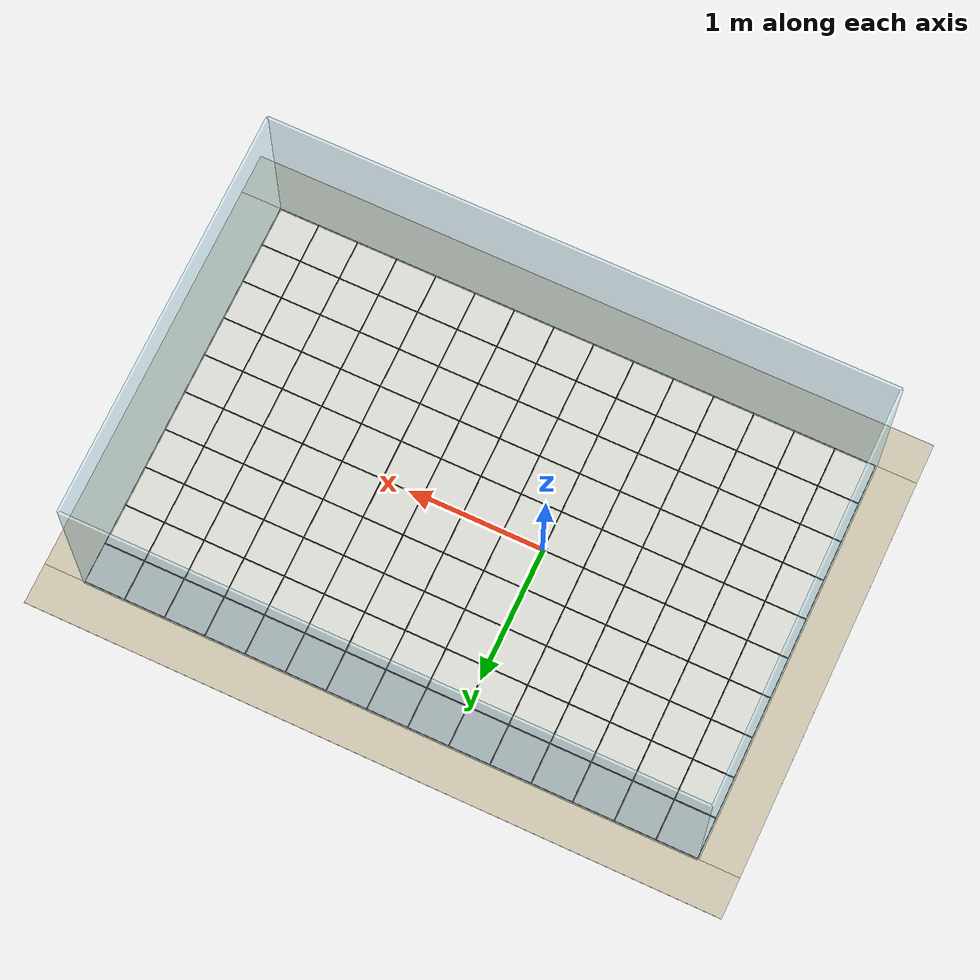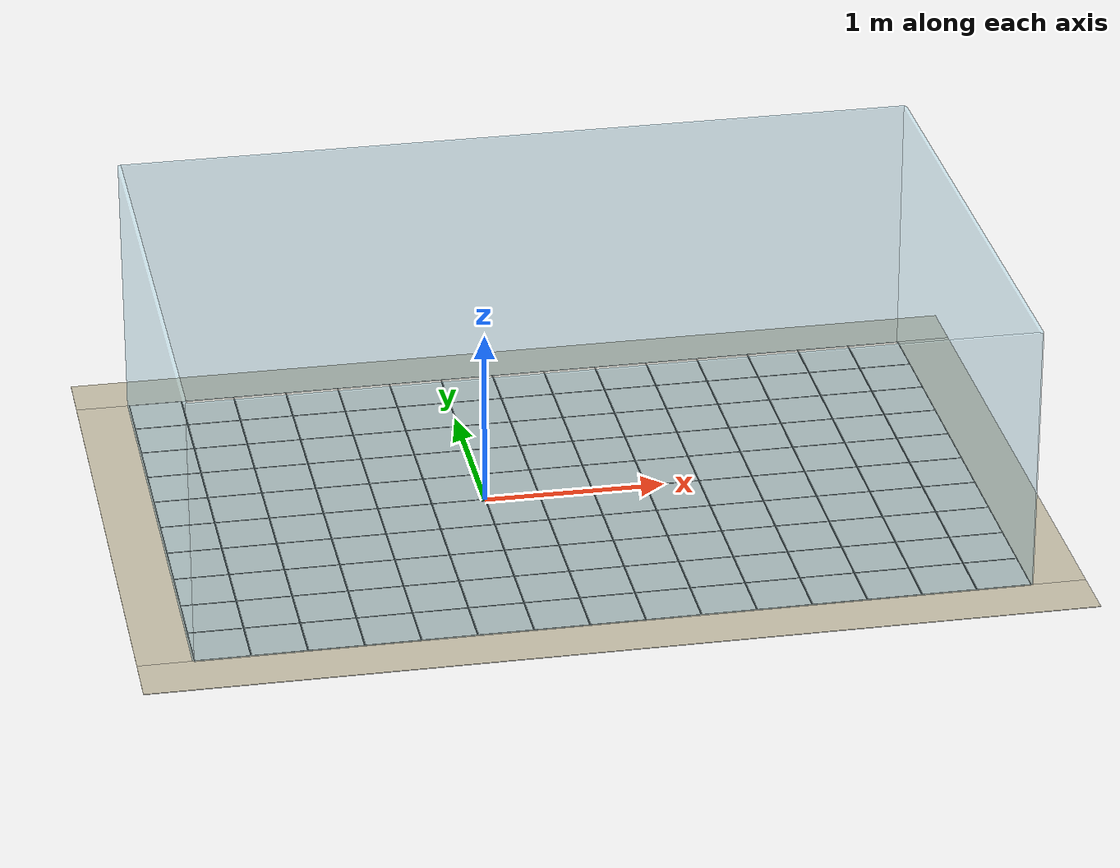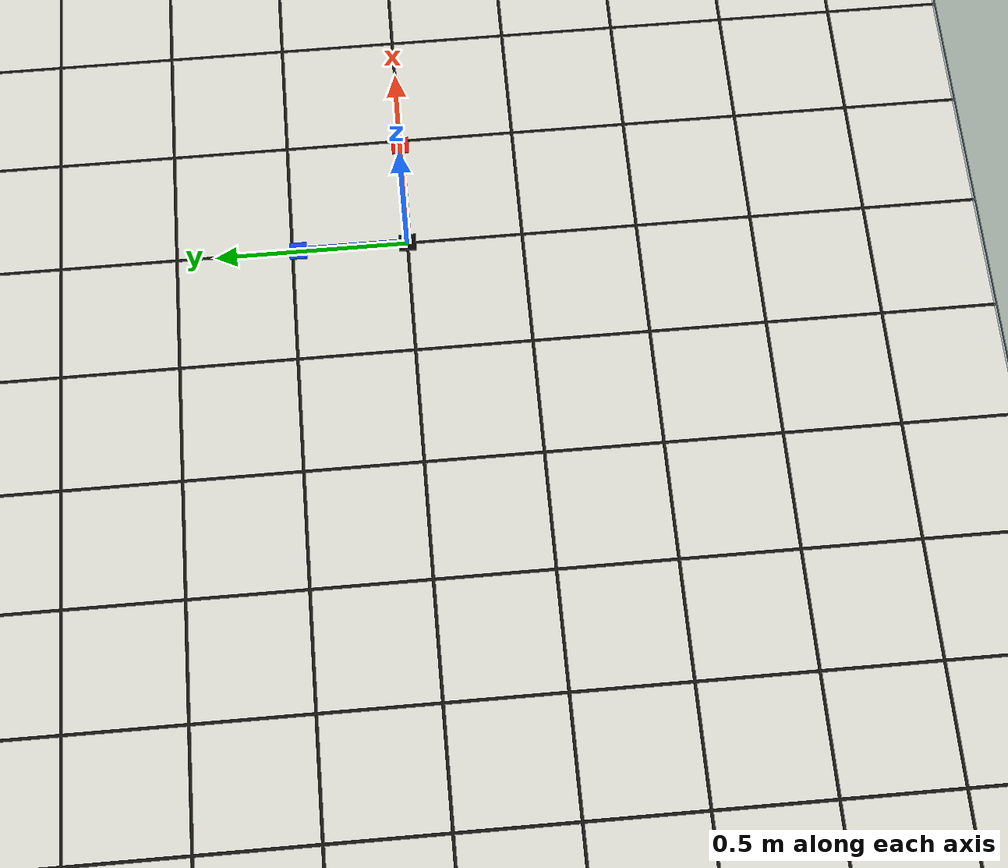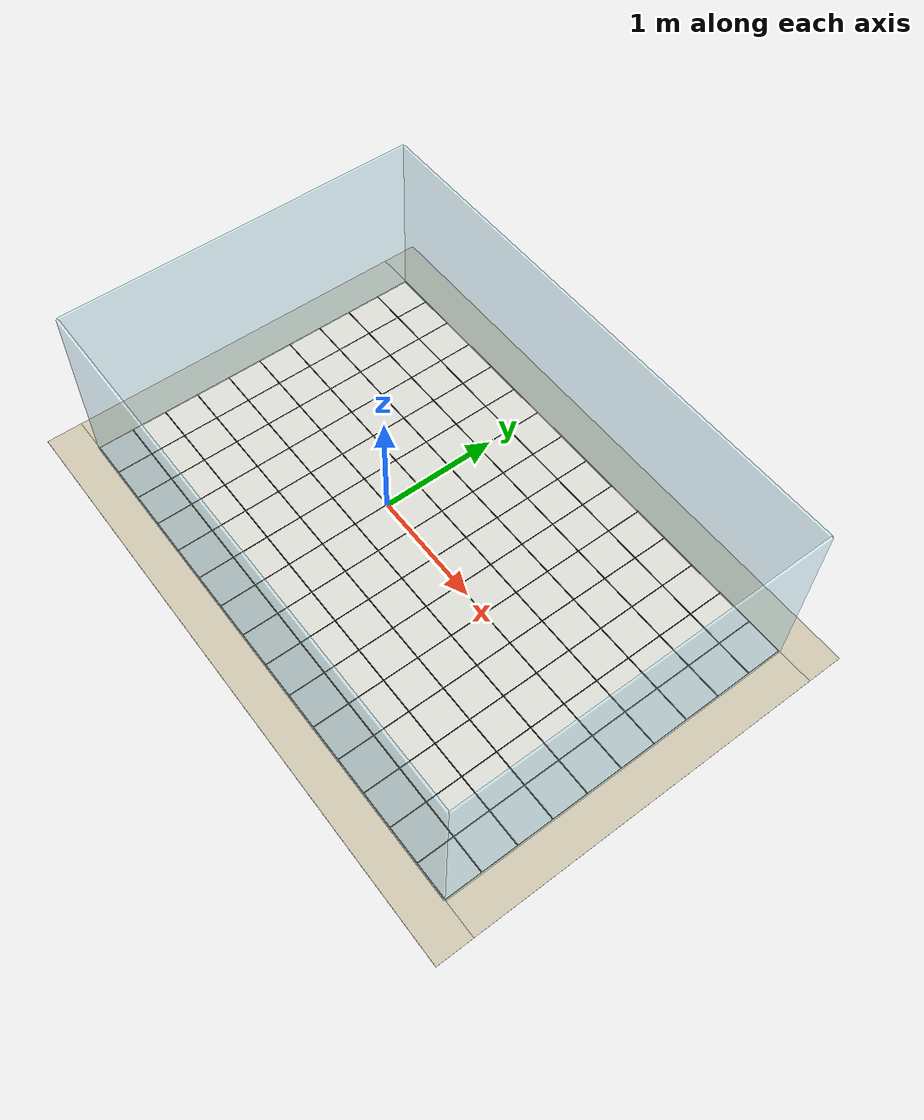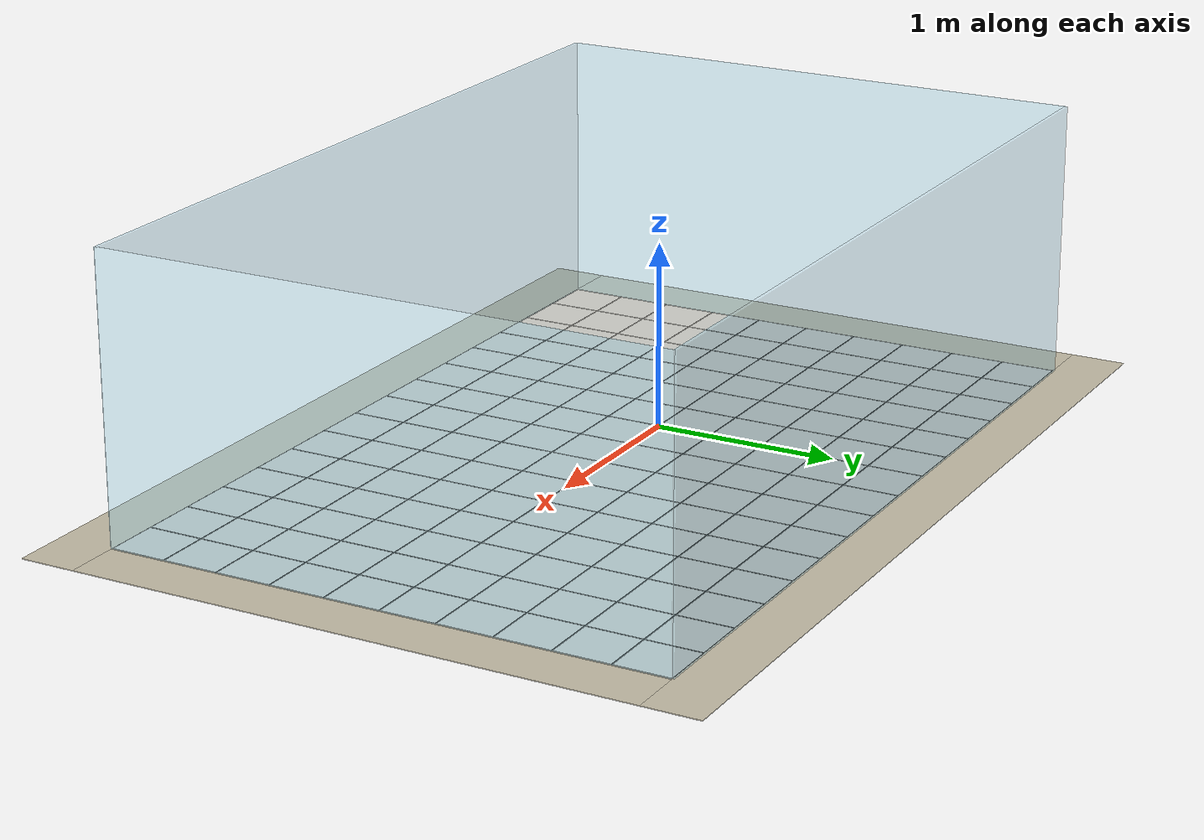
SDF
<?xml version="1.0" ?>
<sdf version="1.7">
  <world name="porcelain_room">
    <gravity>0 0 -9.81</gravity>

    <scene>
      <ambient>0.76 0.76 0.76 1</ambient>
      <background>0.92 0.94 0.96 1</background>
      <shadows>false</shadows>
    </scene>

    <light name="ceiling_light" type="point">
      <pose>0.45 0 3.0 0 0 0</pose>
      <diffuse>0.96 0.94 0.90 1</diffuse>
      <specular>0.28 0.28 0.28 1</specular>
      <attenuation>
        <range>8</range>
        <constant>0.5</constant>
        <linear>0.05</linear>
        <quadratic>0.01</quadratic>
      </attenuation>
      <cast_shadows>false</cast_shadows>
    </light>

    <model name="porcelain_floor">
      <static>true</static>
      <pose>0 0 0 0 0 0</pose>
      <link name="floor">
        <collision name="grout_collision">
          <pose>0.450 0.000 0.001 0 0 0</pose>
          <geometry>
            <box>
              <size>4.500 3.000 0.002</size>
            </box>
          </geometry>
        </collision>
        <visual name="dirty_brown_grout">
          <pose>0.450 0.000 0.001 0 0 0</pose>
          <geometry>
            <box>
              <size>4.500 3.000 0.002</size>
            </box>
          </geometry>
          <material>
            <ambient>0.06 0.05 0.04 1</ambient>
            <diffuse>0.09 0.08 0.06 1</diffuse>
            <specular>0.03 0.03 0.03 1</specular>
          </material>
        </visual>

        <collision name="tile_collision_00_00">
          <pose>-1.650 -1.350 0.002 0 0 0</pose>
          <geometry>
            <box>
              <size>0.292 0.292 0.004</size>
            </box>
          </geometry>
        </collision>
        <visual name="tile_visual_00_00">
          <pose>-1.650 -1.350 0.002 0 0 0</pose>
          <geometry>
            <box>
              <size>0.292 0.292 0.004</size>
            </box>
          </geometry>
          <material>
            <ambient>0.80 0.80 0.78 1</ambient>
            <diffuse>0.88 0.88 0.85 1</diffuse>
            <specular>0.38 0.38 0.36 1</specular>
            <pbr>
              <metal>
                <albedo_map>file:///CrazySim/pfc_ws/worlds/materials/textures/porcelain_tile.png</albedo_map>
                <roughness>0.32</roughness>
                <metalness>0.0</metalness>
              </metal>
            </pbr>
          </material>
        </visual>
        <collision name="tile_collision_00_01">
          <pose>-1.650 -1.050 0.002 0 0 0</pose>
          <geometry>
            <box>
              <size>0.292 0.292 0.004</size>
            </box>
          </geometry>
        </collision>
        <visual name="tile_visual_00_01">
          <pose>-1.650 -1.050 0.002 0 0 0</pose>
          <geometry>
            <box>
              <size>0.292 0.292 0.004</size>
            </box>
          </geometry>
          <material>
            <ambient>0.80 0.80 0.78 1</ambient>
            <diffuse>0.88 0.88 0.85 1</diffuse>
            <specular>0.38 0.38 0.36 1</specular>
            <pbr>
              <metal>
                <albedo_map>file:///CrazySim/pfc_ws/worlds/materials/textures/porcelain_tile.png</albedo_map>
                <roughness>0.32</roughness>
                <metalness>0.0</metalness>
              </metal>
            </pbr>
          </material>
        </visual>
        <collision name="tile_collision_00_02">
          <pose>-1.650 -0.750 0.002 0 0 0</pose>
          <geometry>
            <box>
              <size>0.292 0.292 0.004</size>
            </box>
          </geometry>
        </collision>
        <visual name="tile_visual_00_02">
          <pose>-1.650 -0.750 0.002 0 0 0</pose>
          <geometry>
            <box>
              <size>0.292 0.292 0.004</size>
            </box>
          </geometry>
          <material>
            <ambient>0.80 0.80 0.78 1</ambient>
            <diffuse>0.88 0.88 0.85 1</diffuse>
            <specular>0.38 0.38 0.36 1</specular>
            <pbr>
              <metal>
                <albedo_map>file:///CrazySim/pfc_ws/worlds/materials/textures/porcelain_tile.png</albedo_map>
                <roughness>0.32</roughness>
                <metalness>0.0</metalness>
              </metal>
            </pbr>
          </material>
        </visual>
        <collision name="tile_collision_00_03">
          <pose>-1.650 -0.450 0.002 0 0 0</pose>
          <geometry>
            <box>
              <size>0.292 0.292 0.004</size>
            </box>
          </geometry>
        </collision>
        <visual name="tile_visual_00_03">
          <pose>-1.650 -0.450 0.002 0 0 0</pose>
          <geometry>
            <box>
              <size>0.292 0.292 0.004</size>
            </box>
          </geometry>
          <material>
            <ambient>0.80 0.80 0.78 1</ambient>
            <diffuse>0.88 0.88 0.85 1</diffuse>
            <specular>0.38 0.38 0.36 1</specular>
            <pbr>
              <metal>
                <albedo_map>file:///CrazySim/pfc_ws/worlds/materials/textures/porcelain_tile.png</albedo_map>
                <roughness>0.32</roughness>
                <metalness>0.0</metalness>
              </metal>
            </pbr>
          </material>
        </visual>
        <collision name="tile_collision_00_04">
          <pose>-1.650 -0.150 0.002 0 0 0</pose>
          <geometry>
            <box>
              <size>0.292 0.292 0.004</size>
            </box>
          </geometry>
        </collision>
        <visual name="tile_visual_00_04">
          <pose>-1.650 -0.150 0.002 0 0 0</pose>
          <geometry>
            <box>
              <size>0.292 0.292 0.004</size>
            </box>
          </geometry>
          <material>
            <ambient>0.80 0.80 0.78 1</ambient>
            <diffuse>0.88 0.88 0.85 1</diffuse>
            <specular>0.38 0.38 0.36 1</specular>
            <pbr>
              <metal>
                <albedo_map>file:///CrazySim/pfc_ws/worlds/materials/textures/porcelain_tile.png</albedo_map>
                <roughness>0.32</roughness>
                <metalness>0.0</metalness>
              </metal>
            </pbr>
          </material>
        </visual>
        <collision name="tile_collision_00_05">
          <pose>-1.650 0.150 0.002 0 0 0</pose>
          <geometry>
            <box>
              <size>0.292 0.292 0.004</size>
            </box>
          </geometry>
        </collision>
        <visual name="tile_visual_00_05">
          <pose>-1.650 0.150 0.002 0 0 0</pose>
          <geometry>
            <box>
              <size>0.292 0.292 0.004</size>
            </box>
          </geometry>
          <material>
            <ambient>0.80 0.80 0.78 1</ambient>
            <diffuse>0.88 0.88 0.85 1</diffuse>
            <specular>0.38 0.38 0.36 1</specular>
            <pbr>
              <metal>
                <albedo_map>file:///CrazySim/pfc_ws/worlds/materials/textures/porcelain_tile.png</albedo_map>
                <roughness>0.32</roughness>
                <metalness>0.0</metalness>
              </metal>
            </pbr>
          </material>
        </visual>
        <collision name="tile_collision_00_06">
          <pose>-1.650 0.450 0.002 0 0 0</pose>
          <geometry>
            <box>
              <size>0.292 0.292 0.004</size>
            </box>
          </geometry>
        </collision>
        <visual name="tile_visual_00_06">
          <pose>-1.650 0.450 0.002 0 0 0</pose>
          <geometry>
            <box>
              <size>0.292 0.292 0.004</size>
            </box>
          </geometry>
          <material>
            <ambient>0.80 0.80 0.78 1</ambient>
            <diffuse>0.88 0.88 0.85 1</diffuse>
            <specular>0.38 0.38 0.36 1</specular>
            <pbr>
              <metal>
                <albedo_map>file:///CrazySim/pfc_ws/worlds/materials/textures/porcelain_tile.png</albedo_map>
                <roughness>0.32</roughness>
                <metalness>0.0</metalness>
              </metal>
            </pbr>
          </material>
        </visual>
        <collision name="tile_collision_00_07">
          <pose>-1.650 0.750 0.002 0 0 0</pose>
          <geometry>
            <box>
              <size>0.292 0.292 0.004</size>
            </box>
          </geometry>
        </collision>
        <visual name="tile_visual_00_07">
          <pose>-1.650 0.750 0.002 0 0 0</pose>
          <geometry>
            <box>
              <size>0.292 0.292 0.004</size>
            </box>
          </geometry>
          <material>
            <ambient>0.80 0.80 0.78 1</ambient>
            <diffuse>0.88 0.88 0.85 1</diffuse>
            <specular>0.38 0.38 0.36 1</specular>
            <pbr>
              <metal>
                <albedo_map>file:///CrazySim/pfc_ws/worlds/materials/textures/porcelain_tile.png</albedo_map>
                <roughness>0.32</roughness>
                <metalness>0.0</metalness>
              </metal>
            </pbr>
          </material>
        </visual>
        <collision name="tile_collision_00_08">
          <pose>-1.650 1.050 0.002 0 0 0</pose>
          <geometry>
            <box>
              <size>0.292 0.292 0.004</size>
            </box>
          </geometry>
        </collision>
        <visual name="tile_visual_00_08">
          <pose>-1.650 1.050 0.002 0 0 0</pose>
          <geometry>
            <box>
              <size>0.292 0.292 0.004</size>
            </box>
          </geometry>
          <material>
            <ambient>0.80 0.80 0.78 1</ambient>
            <diffuse>0.88 0.88 0.85 1</diffuse>
            <specular>0.38 0.38 0.36 1</specular>
            <pbr>
              <metal>
                <albedo_map>file:///CrazySim/pfc_ws/worlds/materials/textures/porcelain_tile.png</albedo_map>
                <roughness>0.32</roughness>
                <metalness>0.0</metalness>
              </metal>
            </pbr>
          </material>
        </visual>
        <collision name="tile_collision_00_09">
          <pose>-1.650 1.350 0.002 0 0 0</pose>
          <geometry>
            <box>
              <size>0.292 0.292 0.004</size>
            </box>
          </geometry>
        </collision>
        <visual name="tile_visual_00_09">
          <pose>-1.650 1.350 0.002 0 0 0</pose>
          <geometry>
            <box>
              <size>0.292 0.292 0.004</size>
            </box>
          </geometry>
          <material>
            <ambient>0.80 0.80 0.78 1</ambient>
            <diffuse>0.88 0.88 0.85 1</diffuse>
            <specular>0.38 0.38 0.36 1</specular>
            <pbr>
              <metal>
                <albedo_map>file:///CrazySim/pfc_ws/worlds/materials/textures/porcelain_tile.png</albedo_map>
                <roughness>0.32</roughness>
                <metalness>0.0</metalness>
              </metal>
            </pbr>
          </material>
        </visual>
        <collision name="tile_collision_01_00">
          <pose>-1.350 -1.350 0.002 0 0 0</pose>
          <geometry>
            <box>
              <size>0.292 0.292 0.004</size>
            </box>
          </geometry>
        </collision>
        <visual name="tile_visual_01_00">
          <pose>-1.350 -1.350 0.002 0 0 0</pose>
          <geometry>
            <box>
              <size>0.292 0.292 0.004</size>
            </box>
          </geometry>
          <material>
            <ambient>0.80 0.80 0.78 1</ambient>
            <diffuse>0.88 0.88 0.85 1</diffuse>
            <specular>0.38 0.38 0.36 1</specular>
            <pbr>
              <metal>
                <albedo_map>file:///CrazySim/pfc_ws/worlds/materials/textures/porcelain_tile.png</albedo_map>
                <roughness>0.32</roughness>
                <metalness>0.0</metalness>
              </metal>
            </pbr>
          </material>
        </visual>
        <collision name="tile_collision_01_01">
          <pose>-1.350 -1.050 0.002 0 0 0</pose>
          <geometry>
            <box>
              <size>0.292 0.292 0.004</size>
            </box>
          </geometry>
        </collision>
        <visual name="tile_visual_01_01">
          <pose>-1.350 -1.050 0.002 0 0 0</pose>
          <geometry>
            <box>
              <size>0.292 0.292 0.004</size>
            </box>
          </geometry>
          <material>
            <ambient>0.80 0.80 0.78 1</ambient>
            <diffuse>0.88 0.88 0.85 1</diffuse>
            <specular>0.38 0.38 0.36 1</specular>
            <pbr>
              <metal>
                <albedo_map>file:///CrazySim/pfc_ws/worlds/materials/textures/porcelain_tile.png</albedo_map>
                <roughness>0.32</roughness>
                <metalness>0.0</metalness>
              </metal>
            </pbr>
          </material>
        </visual>
        <collision name="tile_collision_01_02">
          <pose>-1.350 -0.750 0.002 0 0 0</pose>
          <geometry>
            <box>
              <size>0.292 0.292 0.004</size>
            </box>
          </geometry>
        </collision>
        <visual name="tile_visual_01_02">
          <pose>-1.350 -0.750 0.002 0 0 0</pose>
          <geometry>
            <box>
              <size>0.292 0.292 0.004</size>
            </box>
          </geometry>
          <material>
            <ambient>0.80 0.80 0.78 1</ambient>
            <diffuse>0.88 0.88 0.85 1</diffuse>
            <specular>0.38 0.38 0.36 1</specular>
            <pbr>
              <metal>
                <albedo_map>file:///CrazySim/pfc_ws/worlds/materials/textures/porcelain_tile.png</albedo_map>
                <roughness>0.32</roughness>
                <metalness>0.0</metalness>
              </metal>
            </pbr>
          </material>
        </visual>
        <collision name="tile_collision_01_03">
          <pose>-1.350 -0.450 0.002 0 0 0</pose>
          <geometry>
            <box>
              <size>0.292 0.292 0.004</size>
            </box>
          </geometry>
        </collision>
        <visual name="tile_visual_01_03">
          <pose>-1.350 -0.450 0.002 0 0 0</pose>
          <geometry>
            <box>
              <size>0.292 0.292 0.004</size>
            </box>
          </geometry>
          <material>
            <ambient>0.80 0.80 0.78 1</ambient>
            <diffuse>0.88 0.88 0.85 1</diffuse>
            <specular>0.38 0.38 0.36 1</specular>
            <pbr>
              <metal>
                <albedo_map>file:///CrazySim/pfc_ws/worlds/materials/textures/porcelain_tile.png</albedo_map>
                <roughness>0.32</roughness>
                <metalness>0.0</metalness>
              </metal>
            </pbr>
          </material>
        </visual>
        <collision name="tile_collision_01_04">
          <pose>-1.350 -0.150 0.002 0 0 0</pose>
          <geometry>
            <box>
              <size>0.292 0.292 0.004</size>
            </box>
          </geometry>
        </collision>
        <visual name="tile_visual_01_04">
          <pose>-1.350 -0.150 0.002 0 0 0</pose>
          <geometry>
            <box>
              <size>0.292 0.292 0.004</size>
            </box>
          </geometry>
          <material>
            <ambient>0.80 0.80 0.78 1</ambient>
            <diffuse>0.88 0.88 0.85 1</diffuse>
            <specular>0.38 0.38 0.36 1</specular>
            <pbr>
              <metal>
                <albedo_map>file:///CrazySim/pfc_ws/worlds/materials/textures/porcelain_tile.png</albedo_map>
                <roughness>0.32</roughness>
                <metalness>0.0</metalness>
              </metal>
            </pbr>
          </material>
        </visual>
        <collision name="tile_collision_01_05">
          <pose>-1.350 0.150 0.002 0 0 0</pose>
          <geometry>
            <box>
              <size>0.292 0.292 0.004</size>
            </box>
          </geometry>
        </collision>
        <visual name="tile_visual_01_05">
          <pose>-1.350 0.150 0.002 0 0 0</pose>
          <geometry>
            <box>
              <size>0.292 0.292 0.004</size>
            </box>
          </geometry>
          <material>
            <ambient>0.80 0.80 0.78 1</ambient>
            <diffuse>0.88 0.88 0.85 1</diffuse>
            <specular>0.38 0.38 0.36 1</specular>
            <pbr>
              <metal>
                <albedo_map>file:///CrazySim/pfc_ws/worlds/materials/textures/porcelain_tile.png</albedo_map>
                <roughness>0.32</roughness>
                <metalness>0.0</metalness>
              </metal>
            </pbr>
          </material>
        </visual>
        <collision name="tile_collision_01_06">
          <pose>-1.350 0.450 0.002 0 0 0</pose>
          <geometry>
            <box>
              <size>0.292 0.292 0.004</size>
            </box>
          </geometry>
        </collision>
        <visual name="tile_visual_01_06">
          <pose>-1.350 0.450 0.002 0 0 0</pose>
          <geometry>
            <box>
              <size>0.292 0.292 0.004</size>
            </box>
          </geometry>
          <material>
            <ambient>0.80 0.80 0.78 1</ambient>
            <diffuse>0.88 0.88 0.85 1</diffuse>
            <specular>0.38 0.38 0.36 1</specular>
            <pbr>
              <metal>
                <albedo_map>file:///CrazySim/pfc_ws/worlds/materials/textures/porcelain_tile.png</albedo_map>
                <roughness>0.32</roughness>
                <metalness>0.0</metalness>
              </metal>
            </pbr>
          </material>
        </visual>
        <collision name="tile_collision_01_07">
          <pose>-1.350 0.750 0.002 0 0 0</pose>
          <geometry>
            <box>
              <size>0.292 0.292 0.004</size>
            </box>
          </geometry>
        </collision>
        <visual name="tile_visual_01_07">
          <pose>-1.350 0.750 0.002 0 0 0</pose>
          <geometry>
            <box>
              <size>0.292 0.292 0.004</size>
            </box>
          </geometry>
          <material>
            <ambient>0.80 0.80 0.78 1</ambient>
            <diffuse>0.88 0.88 0.85 1</diffuse>
            <specular>0.38 0.38 0.36 1</specular>
            <pbr>
              <metal>
                <albedo_map>file:///CrazySim/pfc_ws/worlds/materials/textures/porcelain_tile.png</albedo_map>
                <roughness>0.32</roughness>
                <metalness>0.0</metalness>
              </metal>
            </pbr>
          </material>
        </visual>
        <collision name="tile_collision_01_08">
          <pose>-1.350 1.050 0.002 0 0 0</pose>
          <geometry>
            <box>
              <size>0.292 0.292 0.004</size>
            </box>
          </geometry>
        </collision>
        <visual name="tile_visual_01_08">
          <pose>-1.350 1.050 0.002 0 0 0</pose>
          <geometry>
            <box>
              <size>0.292 0.292 0.004</size>
            </box>
          </geometry>
          <material>
            <ambient>0.80 0.80 0.78 1</ambient>
            <diffuse>0.88 0.88 0.85 1</diffuse>
            <specular>0.38 0.38 0.36 1</specular>
            <pbr>
              <metal>
                <albedo_map>file:///CrazySim/pfc_ws/worlds/materials/textures/porcelain_tile.png</albedo_map>
                <roughness>0.32</roughness>
                <metalness>0.0</metalness>
              </metal>
            </pbr>
          </material>
        </visual>
        <collision name="tile_collision_01_09">
          <pose>-1.350 1.350 0.002 0 0 0</pose>
          <geometry>
            <box>
              <size>0.292 0.292 0.004</size>
            </box>
          </geometry>
        </collision>
        <visual name="tile_visual_01_09">
          <pose>-1.350 1.350 0.002 0 0 0</pose>
          <geometry>
            <box>
              <size>0.292 0.292 0.004</size>
            </box>
          </geometry>
          <material>
            <ambient>0.80 0.80 0.78 1</ambient>
            <diffuse>0.88 0.88 0.85 1</diffuse>
            <specular>0.38 0.38 0.36 1</specular>
            <pbr>
              <metal>
                <albedo_map>file:///CrazySim/pfc_ws/worlds/materials/textures/porcelain_tile.png</albedo_map>
                <roughness>0.32</roughness>
                <metalness>0.0</metalness>
              </metal>
            </pbr>
          </material>
        </visual>
        <collision name="tile_collision_02_00">
          <pose>-1.050 -1.350 0.002 0 0 0</pose>
          <geometry>
            <box>
              <size>0.292 0.292 0.004</size>
            </box>
          </geometry>
        </collision>
        <visual name="tile_visual_02_00">
          <pose>-1.050 -1.350 0.002 0 0 0</pose>
          <geometry>
            <box>
              <size>0.292 0.292 0.004</size>
            </box>
          </geometry>
          <material>
            <ambient>0.80 0.80 0.78 1</ambient>
            <diffuse>0.88 0.88 0.85 1</diffuse>
            <specular>0.38 0.38 0.36 1</specular>
            <pbr>
              <metal>
                <albedo_map>file:///CrazySim/pfc_ws/worlds/materials/textures/porcelain_tile.png</albedo_map>
                <roughness>0.32</roughness>
                <metalness>0.0</metalness>
              </metal>
            </pbr>
          </material>
        </visual>
        <collision name="tile_collision_02_01">
          <pose>-1.050 -1.050 0.002 0 0 0</pose>
          <geometry>
            <box>
              <size>0.292 0.292 0.004</size>
            </box>
          </geometry>
        </collision>
        <visual name="tile_visual_02_01">
          <pose>-1.050 -1.050 0.002 0 0 0</pose>
          <geometry>
            <box>
              <size>0.292 0.292 0.004</size>
            </box>
          </geometry>
          <material>
            <ambient>0.80 0.80 0.78 1</ambient>
            <diffuse>0.88 0.88 0.85 1</diffuse>
            <specular>0.38 0.38 0.36 1</specular>
            <pbr>
              <metal>
                <albedo_map>file:///CrazySim/pfc_ws/worlds/materials/textures/porcelain_tile.png</albedo_map>
                <roughness>0.32</roughness>
                <metalness>0.0</metalness>
              </metal>
            </pbr>
          </material>
        </visual>
        <collision name="tile_collision_02_02">
          <pose>-1.050 -0.750 0.002 0 0 0</pose>
          <geometry>
            <box>
              <size>0.292 0.292 0.004</size>
            </box>
          </geometry>
        </collision>
        <visual name="tile_visual_02_02">
          <pose>-1.050 -0.750 0.002 0 0 0</pose>
          <geometry>
            <box>
              <size>0.292 0.292 0.004</size>
            </box>
          </geometry>
          <material>
            <ambient>0.80 0.80 0.78 1</ambient>
            <diffuse>0.88 0.88 0.85 1</diffuse>
            <specular>0.38 0.38 0.36 1</specular>
            <pbr>
              <metal>
                <albedo_map>file:///CrazySim/pfc_ws/worlds/materials/textures/porcelain_tile.png</albedo_map>
                <roughness>0.32</roughness>
                <metalness>0.0</metalness>
              </metal>
            </pbr>
          </material>
        </visual>
        <collision name="tile_collision_02_03">
          <pose>-1.050 -0.450 0.002 0 0 0</pose>
          <geometry>
            <box>
              <size>0.292 0.292 0.004</size>
            </box>
          </geometry>
        </collision>
        <visual name="tile_visual_02_03">
          <pose>-1.050 -0.450 0.002 0 0 0</pose>
          <geometry>
            <box>
              <size>0.292 0.292 0.004</size>
            </box>
          </geometry>
          <material>
            <ambient>0.80 0.80 0.78 1</ambient>
            <diffuse>0.88 0.88 0.85 1</diffuse>
            <specular>0.38 0.38 0.36 1</specular>
            <pbr>
              <metal>
                <albedo_map>file:///CrazySim/pfc_ws/worlds/materials/textures/porcelain_tile.png</albedo_map>
                <roughness>0.32</roughness>
                <metalness>0.0</metalness>
              </metal>
            </pbr>
          </material>
        </visual>
        <collision name="tile_collision_02_04">
          <pose>-1.050 -0.150 0.002 0 0 0</pose>
          <geometry>
            <box>
              <size>0.292 0.292 0.004</size>
            </box>
          </geometry>
        </collision>
        <visual name="tile_visual_02_04">
          <pose>-1.050 -0.150 0.002 0 0 0</pose>
          <geometry>
            <box>
              <size>0.292 0.292 0.004</size>
            </box>
          </geometry>
          <material>
            <ambient>0.80 0.80 0.78 1</ambient>
            <diffuse>0.88 0.88 0.85 1</diffuse>
            <specular>0.38 0.38 0.36 1</specular>
            <pbr>
              <metal>
                <albedo_map>file:///CrazySim/pfc_ws/worlds/materials/textures/porcelain_tile.png</albedo_map>
                <roughness>0.32</roughness>
                <metalness>0.0</metalness>
              </metal>
            </pbr>
          </material>
        </visual>
        <collision name="tile_collision_02_05">
          <pose>-1.050 0.150 0.002 0 0 0</pose>
          <geometry>
            <box>
              <size>0.292 0.292 0.004</size>
            </box>
          </geometry>
        </collision>
        <visual name="tile_visual_02_05">
          <pose>-1.050 0.150 0.002 0 0 0</pose>
          <geometry>
            <box>
              <size>0.292 0.292 0.004</size>
            </box>
          </geometry>
          <material>
            <ambient>0.80 0.80 0.78 1</ambient>
            <diffuse>0.88 0.88 0.85 1</diffuse>
            <specular>0.38 0.38 0.36 1</specular>
            <pbr>
              <metal>
                <albedo_map>file:///CrazySim/pfc_ws/worlds/materials/textures/porcelain_tile.png</albedo_map>
                <roughness>0.32</roughness>
                <metalness>0.0</metalness>
              </metal>
            </pbr>
          </material>
        </visual>
        <collision name="tile_collision_02_06">
          <pose>-1.050 0.450 0.002 0 0 0</pose>
          <geometry>
            <box>
              <size>0.292 0.292 0.004</size>
            </box>
          </geometry>
        </collision>
        <visual name="tile_visual_02_06">
          <pose>-1.050 0.450 0.002 0 0 0</pose>
          <geometry>
            <box>
              <size>0.292 0.292 0.004</size>
            </box>
          </geometry>
          <material>
            <ambient>0.80 0.80 0.78 1</ambient>
            <diffuse>0.88 0.88 0.85 1</diffuse>
            <specular>0.38 0.38 0.36 1</specular>
            <pbr>
              <metal>
                <albedo_map>file:///CrazySim/pfc_ws/worlds/materials/textures/porcelain_tile.png</albedo_map>
                <roughness>0.32</roughness>
                <metalness>0.0</metalness>
              </metal>
            </pbr>
          </material>
        </visual>
        <collision name="tile_collision_02_07">
          <pose>-1.050 0.750 0.002 0 0 0</pose>
          <geometry>
            <box>
              <size>0.292 0.292 0.004</size>
            </box>
          </geometry>
        </collision>
        <visual name="tile_visual_02_07">
          <pose>-1.050 0.750 0.002 0 0 0</pose>
          <geometry>
            <box>
              <size>0.292 0.292 0.004</size>
            </box>
          </geometry>
          <material>
            <ambient>0.80 0.80 0.78 1</ambient>
            <diffuse>0.88 0.88 0.85 1</diffuse>
            <specular>0.38 0.38 0.36 1</specular>
            <pbr>
              <metal>
                <albedo_map>file:///CrazySim/pfc_ws/worlds/materials/textures/porcelain_tile.png</albedo_map>
                <roughness>0.32</roughness>
                <metalness>0.0</metalness>
              </metal>
            </pbr>
          </material>
        </visual>
        <collision name="tile_collision_02_08">
          <pose>-1.050 1.050 0.002 0 0 0</pose>
          <geometry>
            <box>
              <size>0.292 0.292 0.004</size>
            </box>
          </geometry>
        </collision>
        <visual name="tile_visual_02_08">
          <pose>-1.050 1.050 0.002 0 0 0</pose>
          <geometry>
            <box>
              <size>0.292 0.292 0.004</size>
            </box>
          </geometry>
          <material>
            <ambient>0.80 0.80 0.78 1</ambient>
            <diffuse>0.88 0.88 0.85 1</diffuse>
            <specular>0.38 0.38 0.36 1</specular>
            <pbr>
              <metal>
                <albedo_map>file:///CrazySim/pfc_ws/worlds/materials/textures/porcelain_tile.png</albedo_map>
                <roughness>0.32</roughness>
                <metalness>0.0</metalness>
              </metal>
            </pbr>
          </material>
        </visual>
        <collision name="tile_collision_02_09">
          <pose>-1.050 1.350 0.002 0 0 0</pose>
          <geometry>
            <box>
              <size>0.292 0.292 0.004</size>
            </box>
          </geometry>
        </collision>
        <visual name="tile_visual_02_09">
          <pose>-1.050 1.350 0.002 0 0 0</pose>
          <geometry>
            <box>
              <size>0.292 0.292 0.004</size>
            </box>
          </geometry>
          <material>
            <ambient>0.80 0.80 0.78 1</ambient>
            <diffuse>0.88 0.88 0.85 1</diffuse>
            <specular>0.38 0.38 0.36 1</specular>
            <pbr>
              <metal>
                <albedo_map>file:///CrazySim/pfc_ws/worlds/materials/textures/porcelain_tile.png</albedo_map>
                <roughness>0.32</roughness>
                <metalness>0.0</metalness>
              </metal>
            </pbr>
          </material>
        </visual>
        <collision name="tile_collision_03_00">
          <pose>-0.750 -1.350 0.002 0 0 0</pose>
          <geometry>
            <box>
              <size>0.292 0.292 0.004</size>
            </box>
          </geometry>
        </collision>
        <visual name="tile_visual_03_00">
          <pose>-0.750 -1.350 0.002 0 0 0</pose>
          <geometry>
            <box>
              <size>0.292 0.292 0.004</size>
            </box>
          </geometry>
          <material>
            <ambient>0.80 0.80 0.78 1</ambient>
            <diffuse>0.88 0.88 0.85 1</diffuse>
            <specular>0.38 0.38 0.36 1</specular>
            <pbr>
              <metal>
                <albedo_map>file:///CrazySim/pfc_ws/worlds/materials/textures/porcelain_tile.png</albedo_map>
                <roughness>0.32</roughness>
                <metalness>0.0</metalness>
              </metal>
            </pbr>
          </material>
        </visual>
        <collision name="tile_collision_03_01">
          <pose>-0.750 -1.050 0.002 0 0 0</pose>
          <geometry>
            <box>
              <size>0.292 0.292 0.004</size>
            </box>
          </geometry>
        </collision>
        <visual name="tile_visual_03_01">
          <pose>-0.750 -1.050 0.002 0 0 0</pose>
          <geometry>
            <box>
              <size>0.292 0.292 0.004</size>
            </box>
          </geometry>
          <material>
            <ambient>0.80 0.80 0.78 1</ambient>
            <diffuse>0.88 0.88 0.85 1</diffuse>
            <specular>0.38 0.38 0.36 1</specular>
            <pbr>
              <metal>
                <albedo_map>file:///CrazySim/pfc_ws/worlds/materials/textures/porcelain_tile.png</albedo_map>
                <roughness>0.32</roughness>
                <metalness>0.0</metalness>
              </metal>
            </pbr>
          </material>
        </visual>
        <collision name="tile_collision_03_02">
          <pose>-0.750 -0.750 0.002 0 0 0</pose>
          <geometry>
            <box>
              <size>0.292 0.292 0.004</size>
            </box>
          </geometry>
        </collision>
        <visual name="tile_visual_03_02">
          <pose>-0.750 -0.750 0.002 0 0 0</pose>
          <geometry>
            <box>
              <size>0.292 0.292 0.004</size>
            </box>
          </geometry>
          <material>
            <ambient>0.80 0.80 0.78 1</ambient>
            <diffuse>0.88 0.88 0.85 1</diffuse>
            <specular>0.38 0.38 0.36 1</specular>
            <pbr>
              <metal>
                <albedo_map>file:///CrazySim/pfc_ws/worlds/materials/textures/porcelain_tile.png</albedo_map>
                <roughness>0.32</roughness>
                <metalness>0.0</metalness>
              </metal>
            </pbr>
          </material>
        </visual>
        <collision name="tile_collision_03_03">
          <pose>-0.750 -0.450 0.002 0 0 0</pose>
          <geometry>
            <box>
              <size>0.292 0.292 0.004</size>
            </box>
          </geometry>
        </collision>
        <visual name="tile_visual_03_03">
          <pose>-0.750 -0.450 0.002 0 0 0</pose>
          <geometry>
            <box>
              <size>0.292 0.292 0.004</size>
            </box>
          </geometry>
          <material>
            <ambient>0.80 0.80 0.78 1</ambient>
            <diffuse>0.88 0.88 0.85 1</diffuse>
            <specular>0.38 0.38 0.36 1</specular>
            <pbr>
              <metal>
                <albedo_map>file:///CrazySim/pfc_ws/worlds/materials/textures/porcelain_tile.png</albedo_map>
                <roughness>0.32</roughness>
                <metalness>0.0</metalness>
              </metal>
            </pbr>
          </material>
        </visual>
        <collision name="tile_collision_03_04">
          <pose>-0.750 -0.150 0.002 0 0 0</pose>
          <geometry>
            <box>
              <size>0.292 0.292 0.004</size>
            </box>
          </geometry>
        </collision>
        <visual name="tile_visual_03_04">
          <pose>-0.750 -0.150 0.002 0 0 0</pose>
          <geometry>
            <box>
              <size>0.292 0.292 0.004</size>
            </box>
          </geometry>
          <material>
            <ambient>0.80 0.80 0.78 1</ambient>
            <diffuse>0.88 0.88 0.85 1</diffuse>
            <specular>0.38 0.38 0.36 1</specular>
            <pbr>
              <metal>
                <albedo_map>file:///CrazySim/pfc_ws/worlds/materials/textures/porcelain_tile.png</albedo_map>
                <roughness>0.32</roughness>
                <metalness>0.0</metalness>
              </metal>
            </pbr>
          </material>
        </visual>
        <collision name="tile_collision_03_05">
          <pose>-0.750 0.150 0.002 0 0 0</pose>
          <geometry>
            <box>
              <size>0.292 0.292 0.004</size>
            </box>
          </geometry>
        </collision>
        <visual name="tile_visual_03_05">
          <pose>-0.750 0.150 0.002 0 0 0</pose>
          <geometry>
            <box>
              <size>0.292 0.292 0.004</size>
            </box>
          </geometry>
          <material>
            <ambient>0.80 0.80 0.78 1</ambient>
            <diffuse>0.88 0.88 0.85 1</diffuse>
            <specular>0.38 0.38 0.36 1</specular>
            <pbr>
              <metal>
                <albedo_map>file:///CrazySim/pfc_ws/worlds/materials/textures/porcelain_tile.png</albedo_map>
                <roughness>0.32</roughness>
                <metalness>0.0</metalness>
              </metal>
            </pbr>
          </material>
        </visual>
        <collision name="tile_collision_03_06">
          <pose>-0.750 0.450 0.002 0 0 0</pose>
          <geometry>
            <box>
              <size>0.292 0.292 0.004</size>
            </box>
          </geometry>
        </collision>
        <visual name="tile_visual_03_06">
          <pose>-0.750 0.450 0.002 0 0 0</pose>
          <geometry>
            <box>
              <size>0.292 0.292 0.004</size>
            </box>
          </geometry>
          <material>
            <ambient>0.80 0.80 0.78 1</ambient>
            <diffuse>0.88 0.88 0.85 1</diffuse>
            <specular>0.38 0.38 0.36 1</specular>
            <pbr>
              <metal>
                <albedo_map>file:///CrazySim/pfc_ws/worlds/materials/textures/porcelain_tile.png</albedo_map>
                <roughness>0.32</roughness>
                <metalness>0.0</metalness>
              </metal>
            </pbr>
          </material>
        </visual>
        <collision name="tile_collision_03_07">
          <pose>-0.750 0.750 0.002 0 0 0</pose>
          <geometry>
            <box>
              <size>0.292 0.292 0.004</size>
            </box>
          </geometry>
        </collision>
        <visual name="tile_visual_03_07">
          <pose>-0.750 0.750 0.002 0 0 0</pose>
          <geometry>
            <box>
              <size>0.292 0.292 0.004</size>
            </box>
          </geometry>
          <material>
            <ambient>0.80 0.80 0.78 1</ambient>
            <diffuse>0.88 0.88 0.85 1</diffuse>
            <specular>0.38 0.38 0.36 1</specular>
            <pbr>
              <metal>
                <albedo_map>file:///CrazySim/pfc_ws/worlds/materials/textures/porcelain_tile.png</albedo_map>
                <roughness>0.32</roughness>
                <metalness>0.0</metalness>
              </metal>
            </pbr>
          </material>
        </visual>
        <collision name="tile_collision_03_08">
          <pose>-0.750 1.050 0.002 0 0 0</pose>
          <geometry>
            <box>
              <size>0.292 0.292 0.004</size>
            </box>
          </geometry>
        </collision>
        <visual name="tile_visual_03_08">
          <pose>-0.750 1.050 0.002 0 0 0</pose>
          <geometry>
            <box>
              <size>0.292 0.292 0.004</size>
            </box>
          </geometry>
          <material>
            <ambient>0.80 0.80 0.78 1</ambient>
            <diffuse>0.88 0.88 0.85 1</diffuse>
            <specular>0.38 0.38 0.36 1</specular>
            <pbr>
              <metal>
                <albedo_map>file:///CrazySim/pfc_ws/worlds/materials/textures/porcelain_tile.png</albedo_map>
                <roughness>0.32</roughness>
                <metalness>0.0</metalness>
              </metal>
            </pbr>
          </material>
        </visual>
        <collision name="tile_collision_03_09">
          <pose>-0.750 1.350 0.002 0 0 0</pose>
          <geometry>
            <box>
              <size>0.292 0.292 0.004</size>
            </box>
          </geometry>
        </collision>
        <visual name="tile_visual_03_09">
          <pose>-0.750 1.350 0.002 0 0 0</pose>
          <geometry>
            <box>
              <size>0.292 0.292 0.004</size>
            </box>
          </geometry>
          <material>
            <ambient>0.80 0.80 0.78 1</ambient>
            <diffuse>0.88 0.88 0.85 1</diffuse>
            <specular>0.38 0.38 0.36 1</specular>
            <pbr>
              <metal>
                <albedo_map>file:///CrazySim/pfc_ws/worlds/materials/textures/porcelain_tile.png</albedo_map>
                <roughness>0.32</roughness>
                <metalness>0.0</metalness>
              </metal>
            </pbr>
          </material>
        </visual>
        <collision name="tile_collision_04_00">
          <pose>-0.450 -1.350 0.002 0 0 0</pose>
          <geometry>
            <box>
              <size>0.292 0.292 0.004</size>
            </box>
          </geometry>
        </collision>
        <visual name="tile_visual_04_00">
          <pose>-0.450 -1.350 0.002 0 0 0</pose>
          <geometry>
            <box>
              <size>0.292 0.292 0.004</size>
            </box>
          </geometry>
          <material>
            <ambient>0.80 0.80 0.78 1</ambient>
            <diffuse>0.88 0.88 0.85 1</diffuse>
            <specular>0.38 0.38 0.36 1</specular>
            <pbr>
              <metal>
                <albedo_map>file:///CrazySim/pfc_ws/worlds/materials/textures/porcelain_tile.png</albedo_map>
                <roughness>0.32</roughness>
                <metalness>0.0</metalness>
              </metal>
            </pbr>
          </material>
        </visual>
        <collision name="tile_collision_04_01">
          <pose>-0.450 -1.050 0.002 0 0 0</pose>
          <geometry>
            <box>
              <size>0.292 0.292 0.004</size>
            </box>
          </geometry>
        </collision>
        <visual name="tile_visual_04_01">
          <pose>-0.450 -1.050 0.002 0 0 0</pose>
          <geometry>
            <box>
              <size>0.292 0.292 0.004</size>
            </box>
          </geometry>
          <material>
            <ambient>0.80 0.80 0.78 1</ambient>
            <diffuse>0.88 0.88 0.85 1</diffuse>
            <specular>0.38 0.38 0.36 1</specular>
            <pbr>
              <metal>
                <albedo_map>file:///CrazySim/pfc_ws/worlds/materials/textures/porcelain_tile.png</albedo_map>
                <roughness>0.32</roughness>
                <metalness>0.0</metalness>
              </metal>
            </pbr>
          </material>
        </visual>
        <collision name="tile_collision_04_02">
          <pose>-0.450 -0.750 0.002 0 0 0</pose>
          <geometry>
            <box>
              <size>0.292 0.292 0.004</size>
            </box>
          </geometry>
        </collision>
        <visual name="tile_visual_04_02">
          <pose>-0.450 -0.750 0.002 0 0 0</pose>
          <geometry>
            <box>
              <size>0.292 0.292 0.004</size>
            </box>
          </geometry>
          <material>
            <ambient>0.80 0.80 0.78 1</ambient>
            <diffuse>0.88 0.88 0.85 1</diffuse>
            <specular>0.38 0.38 0.36 1</specular>
            <pbr>
              <metal>
                <albedo_map>file:///CrazySim/pfc_ws/worlds/materials/textures/porcelain_tile.png</albedo_map>
                <roughness>0.32</roughness>
                <metalness>0.0</metalness>
              </metal>
            </pbr>
          </material>
        </visual>
        <collision name="tile_collision_04_03">
          <pose>-0.450 -0.450 0.002 0 0 0</pose>
          <geometry>
            <box>
              <size>0.292 0.292 0.004</size>
            </box>
          </geometry>
        </collision>
        <visual name="tile_visual_04_03">
          <pose>-0.450 -0.450 0.002 0 0 0</pose>
          <geometry>
            <box>
              <size>0.292 0.292 0.004</size>
            </box>
          </geometry>
          <material>
            <ambient>0.80 0.80 0.78 1</ambient>
            <diffuse>0.88 0.88 0.85 1</diffuse>
            <specular>0.38 0.38 0.36 1</specular>
            <pbr>
              <metal>
                <albedo_map>file:///CrazySim/pfc_ws/worlds/materials/textures/porcelain_tile.png</albedo_map>
                <roughness>0.32</roughness>
                <metalness>0.0</metalness>
              </metal>
            </pbr>
          </material>
        </visual>
        <collision name="tile_collision_04_04">
          <pose>-0.450 -0.150 0.002 0 0 0</pose>
          <geometry>
            <box>
              <size>0.292 0.292 0.004</size>
            </box>
          </geometry>
        </collision>
        <visual name="tile_visual_04_04">
          <pose>-0.450 -0.150 0.002 0 0 0</pose>
          <geometry>
            <box>
              <size>0.292 0.292 0.004</size>
            </box>
          </geometry>
          <material>
            <ambient>0.80 0.80 0.78 1</ambient>
            <diffuse>0.88 0.88 0.85 1</diffuse>
            <specular>0.38 0.38 0.36 1</specular>
            <pbr>
              <metal>
                <albedo_map>file:///CrazySim/pfc_ws/worlds/materials/textures/porcelain_tile.png</albedo_map>
                <roughness>0.32</roughness>
                <metalness>0.0</metalness>
              </metal>
            </pbr>
          </material>
        </visual>
        <collision name="tile_collision_04_05">
          <pose>-0.450 0.150 0.002 0 0 0</pose>
          <geometry>
            <box>
              <size>0.292 0.292 0.004</size>
            </box>
          </geometry>
        </collision>
        <visual name="tile_visual_04_05">
          <pose>-0.450 0.150 0.002 0 0 0</pose>
          <geometry>
            <box>
              <size>0.292 0.292 0.004</size>
            </box>
          </geometry>
          <material>
            <ambient>0.80 0.80 0.78 1</ambient>
            <diffuse>0.88 0.88 0.85 1</diffuse>
            <specular>0.38 0.38 0.36 1</specular>
            <pbr>
              <metal>
                <albedo_map>file:///CrazySim/pfc_ws/worlds/materials/textures/porcelain_tile.png</albedo_map>
                <roughness>0.32</roughness>
                <metalness>0.0</metalness>
              </metal>
            </pbr>
          </material>
        </visual>
        <collision name="tile_collision_04_06">
          <pose>-0.450 0.450 0.002 0 0 0</pose>
          <geometry>
            <box>
              <size>0.292 0.292 0.004</size>
            </box>
          </geometry>
        </collision>
        <visual name="tile_visual_04_06">
          <pose>-0.450 0.450 0.002 0 0 0</pose>
          <geometry>
            <box>
              <size>0.292 0.292 0.004</size>
            </box>
          </geometry>
          <material>
            <ambient>0.80 0.80 0.78 1</ambient>
            <diffuse>0.88 0.88 0.85 1</diffuse>
            <specular>0.38 0.38 0.36 1</specular>
            <pbr>
              <metal>
                <albedo_map>file:///CrazySim/pfc_ws/worlds/materials/textures/porcelain_tile.png</albedo_map>
                <roughness>0.32</roughness>
                <metalness>0.0</metalness>
              </metal>
            </pbr>
          </material>
        </visual>
        <collision name="tile_collision_04_07">
          <pose>-0.450 0.750 0.002 0 0 0</pose>
          <geometry>
            <box>
              <size>0.292 0.292 0.004</size>
            </box>
          </geometry>
        </collision>
        <visual name="tile_visual_04_07">
          <pose>-0.450 0.750 0.002 0 0 0</pose>
          <geometry>
            <box>
              <size>0.292 0.292 0.004</size>
            </box>
          </geometry>
          <material>
            <ambient>0.80 0.80 0.78 1</ambient>
            <diffuse>0.88 0.88 0.85 1</diffuse>
            <specular>0.38 0.38 0.36 1</specular>
            <pbr>
              <metal>
                <albedo_map>file:///CrazySim/pfc_ws/worlds/materials/textures/porcelain_tile.png</albedo_map>
                <roughness>0.32</roughness>
                <metalness>0.0</metalness>
              </metal>
            </pbr>
          </material>
        </visual>
        <collision name="tile_collision_04_08">
          <pose>-0.450 1.050 0.002 0 0 0</pose>
          <geometry>
            <box>
              <size>0.292 0.292 0.004</size>
            </box>
          </geometry>
        </collision>
        <visual name="tile_visual_04_08">
          <pose>-0.450 1.050 0.002 0 0 0</pose>
          <geometry>
            <box>
              <size>0.292 0.292 0.004</size>
            </box>
          </geometry>
          <material>
            <ambient>0.80 0.80 0.78 1</ambient>
            <diffuse>0.88 0.88 0.85 1</diffuse>
            <specular>0.38 0.38 0.36 1</specular>
            <pbr>
              <metal>
                <albedo_map>file:///CrazySim/pfc_ws/worlds/materials/textures/porcelain_tile.png</albedo_map>
                <roughness>0.32</roughness>
                <metalness>0.0</metalness>
              </metal>
            </pbr>
          </material>
        </visual>
        <collision name="tile_collision_04_09">
          <pose>-0.450 1.350 0.002 0 0 0</pose>
          <geometry>
            <box>
              <size>0.292 0.292 0.004</size>
            </box>
          </geometry>
        </collision>
        <visual name="tile_visual_04_09">
          <pose>-0.450 1.350 0.002 0 0 0</pose>
          <geometry>
            <box>
              <size>0.292 0.292 0.004</size>
            </box>
          </geometry>
          <material>
            <ambient>0.80 0.80 0.78 1</ambient>
            <diffuse>0.88 0.88 0.85 1</diffuse>
            <specular>0.38 0.38 0.36 1</specular>
            <pbr>
              <metal>
                <albedo_map>file:///CrazySim/pfc_ws/worlds/materials/textures/porcelain_tile.png</albedo_map>
                <roughness>0.32</roughness>
                <metalness>0.0</metalness>
              </metal>
            </pbr>
          </material>
        </visual>
        <collision name="tile_collision_05_00">
          <pose>-0.150 -1.350 0.002 0 0 0</pose>
          <geometry>
            <box>
              <size>0.292 0.292 0.004</size>
            </box>
          </geometry>
        </collision>
        <visual name="tile_visual_05_00">
          <pose>-0.150 -1.350 0.002 0 0 0</pose>
          <geometry>
            <box>
              <size>0.292 0.292 0.004</size>
            </box>
          </geometry>
          <material>
            <ambient>0.80 0.80 0.78 1</ambient>
            <diffuse>0.88 0.88 0.85 1</diffuse>
            <specular>0.38 0.38 0.36 1</specular>
            <pbr>
              <metal>
                <albedo_map>file:///CrazySim/pfc_ws/worlds/materials/textures/porcelain_tile.png</albedo_map>
                <roughness>0.32</roughness>
                <metalness>0.0</metalness>
              </metal>
            </pbr>
          </material>
        </visual>
        <collision name="tile_collision_05_01">
          <pose>-0.150 -1.050 0.002 0 0 0</pose>
          <geometry>
            <box>
              <size>0.292 0.292 0.004</size>
            </box>
          </geometry>
        </collision>
        <visual name="tile_visual_05_01">
          <pose>-0.150 -1.050 0.002 0 0 0</pose>
          <geometry>
            <box>
              <size>0.292 0.292 0.004</size>
            </box>
          </geometry>
          <material>
            <ambient>0.80 0.80 0.78 1</ambient>
            <diffuse>0.88 0.88 0.85 1</diffuse>
            <specular>0.38 0.38 0.36 1</specular>
            <pbr>
              <metal>
                <albedo_map>file:///CrazySim/pfc_ws/worlds/materials/textures/porcelain_tile.png</albedo_map>
                <roughness>0.32</roughness>
                <metalness>0.0</metalness>
              </metal>
            </pbr>
          </material>
        </visual>
        <collision name="tile_collision_05_02">
          <pose>-0.150 -0.750 0.002 0 0 0</pose>
          <geometry>
            <box>
              <size>0.292 0.292 0.004</size>
            </box>
          </geometry>
        </collision>
        <visual name="tile_visual_05_02">
          <pose>-0.150 -0.750 0.002 0 0 0</pose>
          <geometry>
            <box>
              <size>0.292 0.292 0.004</size>
            </box>
          </geometry>
          <material>
            <ambient>0.80 0.80 0.78 1</ambient>
            <diffuse>0.88 0.88 0.85 1</diffuse>
            <specular>0.38 0.38 0.36 1</specular>
            <pbr>
              <metal>
                <albedo_map>file:///CrazySim/pfc_ws/worlds/materials/textures/porcelain_tile.png</albedo_map>
                <roughness>0.32</roughness>
                <metalness>0.0</metalness>
              </metal>
            </pbr>
          </material>
        </visual>
        <collision name="tile_collision_05_03">
          <pose>-0.150 -0.450 0.002 0 0 0</pose>
          <geometry>
            <box>
              <size>0.292 0.292 0.004</size>
            </box>
          </geometry>
        </collision>
        <visual name="tile_visual_05_03">
          <pose>-0.150 -0.450 0.002 0 0 0</pose>
          <geometry>
            <box>
              <size>0.292 0.292 0.004</size>
            </box>
          </geometry>
          <material>
            <ambient>0.80 0.80 0.78 1</ambient>
            <diffuse>0.88 0.88 0.85 1</diffuse>
            <specular>0.38 0.38 0.36 1</specular>
            <pbr>
              <metal>
                <albedo_map>file:///CrazySim/pfc_ws/worlds/materials/textures/porcelain_tile.png</albedo_map>
                <roughness>0.32</roughness>
                <metalness>0.0</metalness>
              </metal>
            </pbr>
          </material>
        </visual>
        <collision name="tile_collision_05_04">
          <pose>-0.150 -0.150 0.002 0 0 0</pose>
          <geometry>
            <box>
              <size>0.292 0.292 0.004</size>
            </box>
          </geometry>
        </collision>
        <visual name="tile_visual_05_04">
          <pose>-0.150 -0.150 0.002 0 0 0</pose>
          <geometry>
            <box>
              <size>0.292 0.292 0.004</size>
            </box>
          </geometry>
          <material>
            <ambient>0.80 0.80 0.78 1</ambient>
            <diffuse>0.88 0.88 0.85 1</diffuse>
            <specular>0.38 0.38 0.36 1</specular>
            <pbr>
              <metal>
                <albedo_map>file:///CrazySim/pfc_ws/worlds/materials/textures/porcelain_tile.png</albedo_map>
                <roughness>0.32</roughness>
                <metalness>0.0</metalness>
              </metal>
            </pbr>
          </material>
        </visual>
        <collision name="tile_collision_05_05">
          <pose>-0.150 0.150 0.002 0 0 0</pose>
          <geometry>
            <box>
              <size>0.292 0.292 0.004</size>
            </box>
          </geometry>
        </collision>
        <visual name="tile_visual_05_05">
          <pose>-0.150 0.150 0.002 0 0 0</pose>
          <geometry>
            <box>
              <size>0.292 0.292 0.004</size>
            </box>
          </geometry>
          <material>
            <ambient>0.80 0.80 0.78 1</ambient>
            <diffuse>0.88 0.88 0.85 1</diffuse>
            <specular>0.38 0.38 0.36 1</specular>
            <pbr>
              <metal>
                <albedo_map>file:///CrazySim/pfc_ws/worlds/materials/textures/porcelain_tile.png</albedo_map>
                <roughness>0.32</roughness>
                <metalness>0.0</metalness>
              </metal>
            </pbr>
          </material>
        </visual>
        <collision name="tile_collision_05_06">
          <pose>-0.150 0.450 0.002 0 0 0</pose>
          <geometry>
            <box>
              <size>0.292 0.292 0.004</size>
            </box>
          </geometry>
        </collision>
        <visual name="tile_visual_05_06">
          <pose>-0.150 0.450 0.002 0 0 0</pose>
          <geometry>
            <box>
              <size>0.292 0.292 0.004</size>
            </box>
          </geometry>
          <material>
            <ambient>0.80 0.80 0.78 1</ambient>
            <diffuse>0.88 0.88 0.85 1</diffuse>
            <specular>0.38 0.38 0.36 1</specular>
            <pbr>
              <metal>
                <albedo_map>file:///CrazySim/pfc_ws/worlds/materials/textures/porcelain_tile.png</albedo_map>
                <roughness>0.32</roughness>
                <metalness>0.0</metalness>
              </metal>
            </pbr>
          </material>
        </visual>
        <collision name="tile_collision_05_07">
          <pose>-0.150 0.750 0.002 0 0 0</pose>
          <geometry>
            <box>
              <size>0.292 0.292 0.004</size>
            </box>
          </geometry>
        </collision>
        <visual name="tile_visual_05_07">
          <pose>-0.150 0.750 0.002 0 0 0</pose>
          <geometry>
            <box>
              <size>0.292 0.292 0.004</size>
            </box>
          </geometry>
          <material>
            <ambient>0.80 0.80 0.78 1</ambient>
            <diffuse>0.88 0.88 0.85 1</diffuse>
            <specular>0.38 0.38 0.36 1</specular>
            <pbr>
              <metal>
                <albedo_map>file:///CrazySim/pfc_ws/worlds/materials/textures/porcelain_tile.png</albedo_map>
                <roughness>0.32</roughness>
                <metalness>0.0</metalness>
              </metal>
            </pbr>
          </material>
        </visual>
        <collision name="tile_collision_05_08">
          <pose>-0.150 1.050 0.002 0 0 0</pose>
          <geometry>
            <box>
              <size>0.292 0.292 0.004</size>
            </box>
          </geometry>
        </collision>
        <visual name="tile_visual_05_08">
          <pose>-0.150 1.050 0.002 0 0 0</pose>
          <geometry>
            <box>
              <size>0.292 0.292 0.004</size>
            </box>
          </geometry>
          <material>
            <ambient>0.80 0.80 0.78 1</ambient>
            <diffuse>0.88 0.88 0.85 1</diffuse>
            <specular>0.38 0.38 0.36 1</specular>
            <pbr>
              <metal>
                <albedo_map>file:///CrazySim/pfc_ws/worlds/materials/textures/porcelain_tile.png</albedo_map>
                <roughness>0.32</roughness>
                <metalness>0.0</metalness>
              </metal>
            </pbr>
          </material>
        </visual>
        <collision name="tile_collision_05_09">
          <pose>-0.150 1.350 0.002 0 0 0</pose>
          <geometry>
            <box>
              <size>0.292 0.292 0.004</size>
            </box>
          </geometry>
        </collision>
        <visual name="tile_visual_05_09">
          <pose>-0.150 1.350 0.002 0 0 0</pose>
          <geometry>
            <box>
              <size>0.292 0.292 0.004</size>
            </box>
          </geometry>
          <material>
            <ambient>0.80 0.80 0.78 1</ambient>
            <diffuse>0.88 0.88 0.85 1</diffuse>
            <specular>0.38 0.38 0.36 1</specular>
            <pbr>
              <metal>
                <albedo_map>file:///CrazySim/pfc_ws/worlds/materials/textures/porcelain_tile.png</albedo_map>
                <roughness>0.32</roughness>
                <metalness>0.0</metalness>
              </metal>
            </pbr>
          </material>
        </visual>
        <collision name="tile_collision_06_00">
          <pose>0.150 -1.350 0.002 0 0 0</pose>
          <geometry>
            <box>
              <size>0.292 0.292 0.004</size>
            </box>
          </geometry>
        </collision>
        <visual name="tile_visual_06_00">
          <pose>0.150 -1.350 0.002 0 0 0</pose>
          <geometry>
            <box>
              <size>0.292 0.292 0.004</size>
            </box>
          </geometry>
          <material>
            <ambient>0.80 0.80 0.78 1</ambient>
            <diffuse>0.88 0.88 0.85 1</diffuse>
            <specular>0.38 0.38 0.36 1</specular>
            <pbr>
              <metal>
                <albedo_map>file:///CrazySim/pfc_ws/worlds/materials/textures/porcelain_tile.png</albedo_map>
                <roughness>0.32</roughness>
                <metalness>0.0</metalness>
              </metal>
            </pbr>
          </material>
        </visual>
        <collision name="tile_collision_06_01">
          <pose>0.150 -1.050 0.002 0 0 0</pose>
          <geometry>
            <box>
              <size>0.292 0.292 0.004</size>
            </box>
          </geometry>
        </collision>
        <visual name="tile_visual_06_01">
          <pose>0.150 -1.050 0.002 0 0 0</pose>
          <geometry>
            <box>
              <size>0.292 0.292 0.004</size>
            </box>
          </geometry>
          <material>
            <ambient>0.80 0.80 0.78 1</ambient>
            <diffuse>0.88 0.88 0.85 1</diffuse>
            <specular>0.38 0.38 0.36 1</specular>
            <pbr>
              <metal>
                <albedo_map>file:///CrazySim/pfc_ws/worlds/materials/textures/porcelain_tile.png</albedo_map>
                <roughness>0.32</roughness>
                <metalness>0.0</metalness>
              </metal>
            </pbr>
          </material>
        </visual>
        <collision name="tile_collision_06_02">
          <pose>0.150 -0.750 0.002 0 0 0</pose>
          <geometry>
            <box>
              <size>0.292 0.292 0.004</size>
            </box>
          </geometry>
        </collision>
        <visual name="tile_visual_06_02">
          <pose>0.150 -0.750 0.002 0 0 0</pose>
          <geometry>
            <box>
              <size>0.292 0.292 0.004</size>
            </box>
          </geometry>
          <material>
            <ambient>0.80 0.80 0.78 1</ambient>
            <diffuse>0.88 0.88 0.85 1</diffuse>
            <specular>0.38 0.38 0.36 1</specular>
            <pbr>
              <metal>
                <albedo_map>file:///CrazySim/pfc_ws/worlds/materials/textures/porcelain_tile.png</albedo_map>
                <roughness>0.32</roughness>
                <metalness>0.0</metalness>
              </metal>
            </pbr>
          </material>
        </visual>
        <collision name="tile_collision_06_03">
          <pose>0.150 -0.450 0.002 0 0 0</pose>
          <geometry>
            <box>
              <size>0.292 0.292 0.004</size>
            </box>
          </geometry>
        </collision>
        <visual name="tile_visual_06_03">
          <pose>0.150 -0.450 0.002 0 0 0</pose>
          <geometry>
            <box>
              <size>0.292 0.292 0.004</size>
            </box>
          </geometry>
          <material>
            <ambient>0.80 0.80 0.78 1</ambient>
            <diffuse>0.88 0.88 0.85 1</diffuse>
            <specular>0.38 0.38 0.36 1</specular>
            <pbr>
              <metal>
                <albedo_map>file:///CrazySim/pfc_ws/worlds/materials/textures/porcelain_tile.png</albedo_map>
                <roughness>0.32</roughness>
                <metalness>0.0</metalness>
              </metal>
            </pbr>
          </material>
        </visual>
        <collision name="tile_collision_06_04">
          <pose>0.150 -0.150 0.002 0 0 0</pose>
          <geometry>
            <box>
              <size>0.292 0.292 0.004</size>
            </box>
          </geometry>
        </collision>
        <visual name="tile_visual_06_04">
          <pose>0.150 -0.150 0.002 0 0 0</pose>
          <geometry>
            <box>
              <size>0.292 0.292 0.004</size>
            </box>
          </geometry>
          <material>
            <ambient>0.80 0.80 0.78 1</ambient>
            <diffuse>0.88 0.88 0.85 1</diffuse>
            <specular>0.38 0.38 0.36 1</specular>
            <pbr>
              <metal>
                <albedo_map>file:///CrazySim/pfc_ws/worlds/materials/textures/porcelain_tile.png</albedo_map>
                <roughness>0.32</roughness>
                <metalness>0.0</metalness>
              </metal>
            </pbr>
          </material>
        </visual>
        <collision name="tile_collision_06_05">
          <pose>0.150 0.150 0.002 0 0 0</pose>
          <geometry>
            <box>
              <size>0.292 0.292 0.004</size>
            </box>
          </geometry>
        </collision>
        <visual name="tile_visual_06_05">
          <pose>0.150 0.150 0.002 0 0 0</pose>
          <geometry>
            <box>
              <size>0.292 0.292 0.004</size>
            </box>
          </geometry>
          <material>
            <ambient>0.80 0.80 0.78 1</ambient>
            <diffuse>0.88 0.88 0.85 1</diffuse>
            <specular>0.38 0.38 0.36 1</specular>
            <pbr>
              <metal>
                <albedo_map>file:///CrazySim/pfc_ws/worlds/materials/textures/porcelain_tile.png</albedo_map>
                <roughness>0.32</roughness>
                <metalness>0.0</metalness>
              </metal>
            </pbr>
          </material>
        </visual>
        <collision name="tile_collision_06_06">
          <pose>0.150 0.450 0.002 0 0 0</pose>
          <geometry>
            <box>
              <size>0.292 0.292 0.004</size>
            </box>
          </geometry>
        </collision>
        <visual name="tile_visual_06_06">
          <pose>0.150 0.450 0.002 0 0 0</pose>
          <geometry>
            <box>
              <size>0.292 0.292 0.004</size>
            </box>
          </geometry>
          <material>
            <ambient>0.80 0.80 0.78 1</ambient>
            <diffuse>0.88 0.88 0.85 1</diffuse>
            <specular>0.38 0.38 0.36 1</specular>
            <pbr>
              <metal>
                <albedo_map>file:///CrazySim/pfc_ws/worlds/materials/textures/porcelain_tile.png</albedo_map>
                <roughness>0.32</roughness>
                <metalness>0.0</metalness>
              </metal>
            </pbr>
          </material>
        </visual>
        <collision name="tile_collision_06_07">
          <pose>0.150 0.750 0.002 0 0 0</pose>
          <geometry>
            <box>
              <size>0.292 0.292 0.004</size>
            </box>
          </geometry>
        </collision>
        <visual name="tile_visual_06_07">
          <pose>0.150 0.750 0.002 0 0 0</pose>
          <geometry>
            <box>
              <size>0.292 0.292 0.004</size>
            </box>
          </geometry>
          <material>
            <ambient>0.80 0.80 0.78 1</ambient>
            <diffuse>0.88 0.88 0.85 1</diffuse>
            <specular>0.38 0.38 0.36 1</specular>
            <pbr>
              <metal>
                <albedo_map>file:///CrazySim/pfc_ws/worlds/materials/textures/porcelain_tile.png</albedo_map>
                <roughness>0.32</roughness>
                <metalness>0.0</metalness>
              </metal>
            </pbr>
          </material>
        </visual>
        <collision name="tile_collision_06_08">
          <pose>0.150 1.050 0.002 0 0 0</pose>
          <geometry>
            <box>
              <size>0.292 0.292 0.004</size>
            </box>
          </geometry>
        </collision>
        <visual name="tile_visual_06_08">
          <pose>0.150 1.050 0.002 0 0 0</pose>
          <geometry>
            <box>
              <size>0.292 0.292 0.004</size>
            </box>
          </geometry>
          <material>
            <ambient>0.80 0.80 0.78 1</ambient>
            <diffuse>0.88 0.88 0.85 1</diffuse>
            <specular>0.38 0.38 0.36 1</specular>
            <pbr>
              <metal>
                <albedo_map>file:///CrazySim/pfc_ws/worlds/materials/textures/porcelain_tile.png</albedo_map>
                <roughness>0.32</roughness>
                <metalness>0.0</metalness>
              </metal>
            </pbr>
          </material>
        </visual>
        <collision name="tile_collision_06_09">
          <pose>0.150 1.350 0.002 0 0 0</pose>
          <geometry>
            <box>
              <size>0.292 0.292 0.004</size>
            </box>
          </geometry>
        </collision>
        <visual name="tile_visual_06_09">
          <pose>0.150 1.350 0.002 0 0 0</pose>
          <geometry>
            <box>
              <size>0.292 0.292 0.004</size>
            </box>
          </geometry>
          <material>
            <ambient>0.80 0.80 0.78 1</ambient>
            <diffuse>0.88 0.88 0.85 1</diffuse>
            <specular>0.38 0.38 0.36 1</specular>
            <pbr>
              <metal>
                <albedo_map>file:///CrazySim/pfc_ws/worlds/materials/textures/porcelain_tile.png</albedo_map>
                <roughness>0.32</roughness>
                <metalness>0.0</metalness>
              </metal>
            </pbr>
          </material>
        </visual>
        <collision name="tile_collision_07_00">
          <pose>0.450 -1.350 0.002 0 0 0</pose>
          <geometry>
            <box>
              <size>0.292 0.292 0.004</size>
            </box>
          </geometry>
        </collision>
        <visual name="tile_visual_07_00">
          <pose>0.450 -1.350 0.002 0 0 0</pose>
          <geometry>
            <box>
              <size>0.292 0.292 0.004</size>
            </box>
          </geometry>
          <material>
            <ambient>0.80 0.80 0.78 1</ambient>
            <diffuse>0.88 0.88 0.85 1</diffuse>
            <specular>0.38 0.38 0.36 1</specular>
            <pbr>
              <metal>
                <albedo_map>file:///CrazySim/pfc_ws/worlds/materials/textures/porcelain_tile.png</albedo_map>
                <roughness>0.32</roughness>
                <metalness>0.0</metalness>
              </metal>
            </pbr>
          </material>
        </visual>
        <collision name="tile_collision_07_01">
          <pose>0.450 -1.050 0.002 0 0 0</pose>
          <geometry>
            <box>
              <size>0.292 0.292 0.004</size>
            </box>
          </geometry>
        </collision>
        <visual name="tile_visual_07_01">
          <pose>0.450 -1.050 0.002 0 0 0</pose>
          <geometry>
            <box>
              <size>0.292 0.292 0.004</size>
            </box>
          </geometry>
          <material>
            <ambient>0.80 0.80 0.78 1</ambient>
            <diffuse>0.88 0.88 0.85 1</diffuse>
            <specular>0.38 0.38 0.36 1</specular>
            <pbr>
              <metal>
                <albedo_map>file:///CrazySim/pfc_ws/worlds/materials/textures/porcelain_tile.png</albedo_map>
                <roughness>0.32</roughness>
                <metalness>0.0</metalness>
              </metal>
            </pbr>
          </material>
        </visual>
        <collision name="tile_collision_07_02">
          <pose>0.450 -0.750 0.002 0 0 0</pose>
          <geometry>
            <box>
              <size>0.292 0.292 0.004</size>
            </box>
          </geometry>
        </collision>
        <visual name="tile_visual_07_02">
          <pose>0.450 -0.750 0.002 0 0 0</pose>
          <geometry>
            <box>
              <size>0.292 0.292 0.004</size>
            </box>
          </geometry>
          <material>
            <ambient>0.80 0.80 0.78 1</ambient>
            <diffuse>0.88 0.88 0.85 1</diffuse>
            <specular>0.38 0.38 0.36 1</specular>
            <pbr>
              <metal>
                <albedo_map>file:///CrazySim/pfc_ws/worlds/materials/textures/porcelain_tile.png</albedo_map>
                <roughness>0.32</roughness>
                <metalness>0.0</metalness>
              </metal>
            </pbr>
          </material>
        </visual>
        <collision name="tile_collision_07_03">
          <pose>0.450 -0.450 0.002 0 0 0</pose>
          <geometry>
            <box>
              <size>0.292 0.292 0.004</size>
            </box>
          </geometry>
        </collision>
        <visual name="tile_visual_07_03">
          <pose>0.450 -0.450 0.002 0 0 0</pose>
          <geometry>
            <box>
              <size>0.292 0.292 0.004</size>
            </box>
          </geometry>
          <material>
            <ambient>0.80 0.80 0.78 1</ambient>
            <diffuse>0.88 0.88 0.85 1</diffuse>
            <specular>0.38 0.38 0.36 1</specular>
            <pbr>
              <metal>
                <albedo_map>file:///CrazySim/pfc_ws/worlds/materials/textures/porcelain_tile.png</albedo_map>
                <roughness>0.32</roughness>
                <metalness>0.0</metalness>
              </metal>
            </pbr>
          </material>
        </visual>
        <collision name="tile_collision_07_04">
          <pose>0.450 -0.150 0.002 0 0 0</pose>
          <geometry>
            <box>
              <size>0.292 0.292 0.004</size>
            </box>
          </geometry>
        </collision>
        <visual name="tile_visual_07_04">
          <pose>0.450 -0.150 0.002 0 0 0</pose>
          <geometry>
            <box>
              <size>0.292 0.292 0.004</size>
            </box>
          </geometry>
          <material>
            <ambient>0.80 0.80 0.78 1</ambient>
            <diffuse>0.88 0.88 0.85 1</diffuse>
            <specular>0.38 0.38 0.36 1</specular>
            <pbr>
              <metal>
                <albedo_map>file:///CrazySim/pfc_ws/worlds/materials/textures/porcelain_tile.png</albedo_map>
                <roughness>0.32</roughness>
                <metalness>0.0</metalness>
              </metal>
            </pbr>
          </material>
        </visual>
        <collision name="tile_collision_07_05">
          <pose>0.450 0.150 0.002 0 0 0</pose>
          <geometry>
            <box>
              <size>0.292 0.292 0.004</size>
            </box>
          </geometry>
        </collision>
        <visual name="tile_visual_07_05">
          <pose>0.450 0.150 0.002 0 0 0</pose>
          <geometry>
            <box>
              <size>0.292 0.292 0.004</size>
            </box>
          </geometry>
          <material>
            <ambient>0.80 0.80 0.78 1</ambient>
            <diffuse>0.88 0.88 0.85 1</diffuse>
            <specular>0.38 0.38 0.36 1</specular>
            <pbr>
              <metal>
                <albedo_map>file:///CrazySim/pfc_ws/worlds/materials/textures/porcelain_tile.png</albedo_map>
                <roughness>0.32</roughness>
                <metalness>0.0</metalness>
              </metal>
            </pbr>
          </material>
        </visual>
        <collision name="tile_collision_07_06">
          <pose>0.450 0.450 0.002 0 0 0</pose>
          <geometry>
            <box>
              <size>0.292 0.292 0.004</size>
            </box>
          </geometry>
        </collision>
        <visual name="tile_visual_07_06">
          <pose>0.450 0.450 0.002 0 0 0</pose>
          <geometry>
            <box>
              <size>0.292 0.292 0.004</size>
            </box>
          </geometry>
          <material>
            <ambient>0.80 0.80 0.78 1</ambient>
            <diffuse>0.88 0.88 0.85 1</diffuse>
            <specular>0.38 0.38 0.36 1</specular>
            <pbr>
              <metal>
                <albedo_map>file:///CrazySim/pfc_ws/worlds/materials/textures/porcelain_tile.png</albedo_map>
                <roughness>0.32</roughness>
                <metalness>0.0</metalness>
              </metal>
            </pbr>
          </material>
        </visual>
        <collision name="tile_collision_07_07">
          <pose>0.450 0.750 0.002 0 0 0</pose>
          <geometry>
            <box>
              <size>0.292 0.292 0.004</size>
            </box>
          </geometry>
        </collision>
        <visual name="tile_visual_07_07">
          <pose>0.450 0.750 0.002 0 0 0</pose>
          <geometry>
            <box>
              <size>0.292 0.292 0.004</size>
            </box>
          </geometry>
          <material>
            <ambient>0.80 0.80 0.78 1</ambient>
            <diffuse>0.88 0.88 0.85 1</diffuse>
            <specular>0.38 0.38 0.36 1</specular>
            <pbr>
              <metal>
                <albedo_map>file:///CrazySim/pfc_ws/worlds/materials/textures/porcelain_tile.png</albedo_map>
                <roughness>0.32</roughness>
                <metalness>0.0</metalness>
              </metal>
            </pbr>
          </material>
        </visual>
        <collision name="tile_collision_07_08">
          <pose>0.450 1.050 0.002 0 0 0</pose>
          <geometry>
            <box>
              <size>0.292 0.292 0.004</size>
            </box>
          </geometry>
        </collision>
        <visual name="tile_visual_07_08">
          <pose>0.450 1.050 0.002 0 0 0</pose>
          <geometry>
            <box>
              <size>0.292 0.292 0.004</size>
            </box>
          </geometry>
          <material>
            <ambient>0.80 0.80 0.78 1</ambient>
            <diffuse>0.88 0.88 0.85 1</diffuse>
            <specular>0.38 0.38 0.36 1</specular>
            <pbr>
              <metal>
                <albedo_map>file:///CrazySim/pfc_ws/worlds/materials/textures/porcelain_tile.png</albedo_map>
                <roughness>0.32</roughness>
                <metalness>0.0</metalness>
              </metal>
            </pbr>
          </material>
        </visual>
        <collision name="tile_collision_07_09">
          <pose>0.450 1.350 0.002 0 0 0</pose>
          <geometry>
            <box>
              <size>0.292 0.292 0.004</size>
            </box>
          </geometry>
        </collision>
        <visual name="tile_visual_07_09">
          <pose>0.450 1.350 0.002 0 0 0</pose>
          <geometry>
            <box>
              <size>0.292 0.292 0.004</size>
            </box>
          </geometry>
          <material>
            <ambient>0.80 0.80 0.78 1</ambient>
            <diffuse>0.88 0.88 0.85 1</diffuse>
            <specular>0.38 0.38 0.36 1</specular>
            <pbr>
              <metal>
                <albedo_map>file:///CrazySim/pfc_ws/worlds/materials/textures/porcelain_tile.png</albedo_map>
                <roughness>0.32</roughness>
                <metalness>0.0</metalness>
              </metal>
            </pbr>
          </material>
        </visual>
        <collision name="tile_collision_08_00">
          <pose>0.750 -1.350 0.002 0 0 0</pose>
          <geometry>
            <box>
              <size>0.292 0.292 0.004</size>
            </box>
          </geometry>
        </collision>
        <visual name="tile_visual_08_00">
          <pose>0.750 -1.350 0.002 0 0 0</pose>
          <geometry>
            <box>
              <size>0.292 0.292 0.004</size>
            </box>
          </geometry>
          <material>
            <ambient>0.80 0.80 0.78 1</ambient>
            <diffuse>0.88 0.88 0.85 1</diffuse>
            <specular>0.38 0.38 0.36 1</specular>
            <pbr>
              <metal>
                <albedo_map>file:///CrazySim/pfc_ws/worlds/materials/textures/porcelain_tile.png</albedo_map>
                <roughness>0.32</roughness>
                <metalness>0.0</metalness>
              </metal>
            </pbr>
          </material>
        </visual>
        <collision name="tile_collision_08_01">
          <pose>0.750 -1.050 0.002 0 0 0</pose>
          <geometry>
            <box>
              <size>0.292 0.292 0.004</size>
            </box>
          </geometry>
        </collision>
        <visual name="tile_visual_08_01">
          <pose>0.750 -1.050 0.002 0 0 0</pose>
          <geometry>
            <box>
              <size>0.292 0.292 0.004</size>
            </box>
          </geometry>
          <material>
            <ambient>0.80 0.80 0.78 1</ambient>
            <diffuse>0.88 0.88 0.85 1</diffuse>
            <specular>0.38 0.38 0.36 1</specular>
            <pbr>
              <metal>
                <albedo_map>file:///CrazySim/pfc_ws/worlds/materials/textures/porcelain_tile.png</albedo_map>
                <roughness>0.32</roughness>
                <metalness>0.0</metalness>
              </metal>
            </pbr>
          </material>
        </visual>
        <collision name="tile_collision_08_02">
          <pose>0.750 -0.750 0.002 0 0 0</pose>
          <geometry>
            <box>
              <size>0.292 0.292 0.004</size>
            </box>
          </geometry>
        </collision>
        <visual name="tile_visual_08_02">
          <pose>0.750 -0.750 0.002 0 0 0</pose>
          <geometry>
            <box>
              <size>0.292 0.292 0.004</size>
            </box>
          </geometry>
          <material>
            <ambient>0.80 0.80 0.78 1</ambient>
            <diffuse>0.88 0.88 0.85 1</diffuse>
            <specular>0.38 0.38 0.36 1</specular>
            <pbr>
              <metal>
                <albedo_map>file:///CrazySim/pfc_ws/worlds/materials/textures/porcelain_tile.png</albedo_map>
                <roughness>0.32</roughness>
                <metalness>0.0</metalness>
              </metal>
            </pbr>
          </material>
        </visual>
        <collision name="tile_collision_08_03">
          <pose>0.750 -0.450 0.002 0 0 0</pose>
          <geometry>
            <box>
              <size>0.292 0.292 0.004</size>
            </box>
          </geometry>
        </collision>
        <visual name="tile_visual_08_03">
          <pose>0.750 -0.450 0.002 0 0 0</pose>
          <geometry>
            <box>
              <size>0.292 0.292 0.004</size>
            </box>
          </geometry>
          <material>
            <ambient>0.80 0.80 0.78 1</ambient>
            <diffuse>0.88 0.88 0.85 1</diffuse>
            <specular>0.38 0.38 0.36 1</specular>
            <pbr>
              <metal>
                <albedo_map>file:///CrazySim/pfc_ws/worlds/materials/textures/porcelain_tile.png</albedo_map>
                <roughness>0.32</roughness>
                <metalness>0.0</metalness>
              </metal>
            </pbr>
          </material>
        </visual>
        <collision name="tile_collision_08_04">
          <pose>0.750 -0.150 0.002 0 0 0</pose>
          <geometry>
            <box>
              <size>0.292 0.292 0.004</size>
            </box>
          </geometry>
        </collision>
        <visual name="tile_visual_08_04">
          <pose>0.750 -0.150 0.002 0 0 0</pose>
          <geometry>
            <box>
              <size>0.292 0.292 0.004</size>
            </box>
          </geometry>
          <material>
            <ambient>0.80 0.80 0.78 1</ambient>
            <diffuse>0.88 0.88 0.85 1</diffuse>
            <specular>0.38 0.38 0.36 1</specular>
            <pbr>
              <metal>
                <albedo_map>file:///CrazySim/pfc_ws/worlds/materials/textures/porcelain_tile.png</albedo_map>
                <roughness>0.32</roughness>
                <metalness>0.0</metalness>
              </metal>
            </pbr>
          </material>
        </visual>
        <collision name="tile_collision_08_05">
          <pose>0.750 0.150 0.002 0 0 0</pose>
          <geometry>
            <box>
              <size>0.292 0.292 0.004</size>
            </box>
          </geometry>
        </collision>
        <visual name="tile_visual_08_05">
          <pose>0.750 0.150 0.002 0 0 0</pose>
          <geometry>
            <box>
              <size>0.292 0.292 0.004</size>
            </box>
          </geometry>
          <material>
            <ambient>0.80 0.80 0.78 1</ambient>
            <diffuse>0.88 0.88 0.85 1</diffuse>
            <specular>0.38 0.38 0.36 1</specular>
            <pbr>
              <metal>
                <albedo_map>file:///CrazySim/pfc_ws/worlds/materials/textures/porcelain_tile.png</albedo_map>
                <roughness>0.32</roughness>
                <metalness>0.0</metalness>
              </metal>
            </pbr>
          </material>
        </visual>
        <collision name="tile_collision_08_06">
          <pose>0.750 0.450 0.002 0 0 0</pose>
          <geometry>
            <box>
              <size>0.292 0.292 0.004</size>
            </box>
          </geometry>
        </collision>
        <visual name="tile_visual_08_06">
          <pose>0.750 0.450 0.002 0 0 0</pose>
          <geometry>
            <box>
              <size>0.292 0.292 0.004</size>
            </box>
          </geometry>
          <material>
            <ambient>0.80 0.80 0.78 1</ambient>
            <diffuse>0.88 0.88 0.85 1</diffuse>
            <specular>0.38 0.38 0.36 1</specular>
            <pbr>
              <metal>
                <albedo_map>file:///CrazySim/pfc_ws/worlds/materials/textures/porcelain_tile.png</albedo_map>
                <roughness>0.32</roughness>
                <metalness>0.0</metalness>
              </metal>
            </pbr>
          </material>
        </visual>
        <collision name="tile_collision_08_07">
          <pose>0.750 0.750 0.002 0 0 0</pose>
          <geometry>
            <box>
              <size>0.292 0.292 0.004</size>
            </box>
          </geometry>
        </collision>
        <visual name="tile_visual_08_07">
          <pose>0.750 0.750 0.002 0 0 0</pose>
          <geometry>
            <box>
              <size>0.292 0.292 0.004</size>
            </box>
          </geometry>
          <material>
            <ambient>0.80 0.80 0.78 1</ambient>
            <diffuse>0.88 0.88 0.85 1</diffuse>
            <specular>0.38 0.38 0.36 1</specular>
            <pbr>
              <metal>
                <albedo_map>file:///CrazySim/pfc_ws/worlds/materials/textures/porcelain_tile.png</albedo_map>
                <roughness>0.32</roughness>
                <metalness>0.0</metalness>
              </metal>
            </pbr>
          </material>
        </visual>
        <collision name="tile_collision_08_08">
          <pose>0.750 1.050 0.002 0 0 0</pose>
          <geometry>
            <box>
              <size>0.292 0.292 0.004</size>
            </box>
          </geometry>
        </collision>
        <visual name="tile_visual_08_08">
          <pose>0.750 1.050 0.002 0 0 0</pose>
          <geometry>
            <box>
              <size>0.292 0.292 0.004</size>
            </box>
          </geometry>
          <material>
            <ambient>0.80 0.80 0.78 1</ambient>
            <diffuse>0.88 0.88 0.85 1</diffuse>
            <specular>0.38 0.38 0.36 1</specular>
            <pbr>
              <metal>
                <albedo_map>file:///CrazySim/pfc_ws/worlds/materials/textures/porcelain_tile.png</albedo_map>
                <roughness>0.32</roughness>
                <metalness>0.0</metalness>
              </metal>
            </pbr>
          </material>
        </visual>
        <collision name="tile_collision_08_09">
          <pose>0.750 1.350 0.002 0 0 0</pose>
          <geometry>
            <box>
              <size>0.292 0.292 0.004</size>
            </box>
          </geometry>
        </collision>
        <visual name="tile_visual_08_09">
          <pose>0.750 1.350 0.002 0 0 0</pose>
          <geometry>
            <box>
              <size>0.292 0.292 0.004</size>
            </box>
          </geometry>
          <material>
            <ambient>0.80 0.80 0.78 1</ambient>
            <diffuse>0.88 0.88 0.85 1</diffuse>
            <specular>0.38 0.38 0.36 1</specular>
            <pbr>
              <metal>
                <albedo_map>file:///CrazySim/pfc_ws/worlds/materials/textures/porcelain_tile.png</albedo_map>
                <roughness>0.32</roughness>
                <metalness>0.0</metalness>
              </metal>
            </pbr>
          </material>
        </visual>
        <collision name="tile_collision_09_00">
          <pose>1.050 -1.350 0.002 0 0 0</pose>
          <geometry>
            <box>
              <size>0.292 0.292 0.004</size>
            </box>
          </geometry>
        </collision>
        <visual name="tile_visual_09_00">
          <pose>1.050 -1.350 0.002 0 0 0</pose>
          <geometry>
            <box>
              <size>0.292 0.292 0.004</size>
            </box>
          </geometry>
          <material>
            <ambient>0.80 0.80 0.78 1</ambient>
            <diffuse>0.88 0.88 0.85 1</diffuse>
            <specular>0.38 0.38 0.36 1</specular>
            <pbr>
              <metal>
                <albedo_map>file:///CrazySim/pfc_ws/worlds/materials/textures/porcelain_tile.png</albedo_map>
                <roughness>0.32</roughness>
                <metalness>0.0</metalness>
              </metal>
            </pbr>
          </material>
        </visual>
        <collision name="tile_collision_09_01">
          <pose>1.050 -1.050 0.002 0 0 0</pose>
          <geometry>
            <box>
              <size>0.292 0.292 0.004</size>
            </box>
          </geometry>
        </collision>
        <visual name="tile_visual_09_01">
          <pose>1.050 -1.050 0.002 0 0 0</pose>
          <geometry>
            <box>
              <size>0.292 0.292 0.004</size>
            </box>
          </geometry>
          <material>
            <ambient>0.80 0.80 0.78 1</ambient>
            <diffuse>0.88 0.88 0.85 1</diffuse>
            <specular>0.38 0.38 0.36 1</specular>
            <pbr>
              <metal>
                <albedo_map>file:///CrazySim/pfc_ws/worlds/materials/textures/porcelain_tile.png</albedo_map>
                <roughness>0.32</roughness>
                <metalness>0.0</metalness>
              </metal>
            </pbr>
          </material>
        </visual>
        <collision name="tile_collision_09_02">
          <pose>1.050 -0.750 0.002 0 0 0</pose>
          <geometry>
            <box>
              <size>0.292 0.292 0.004</size>
            </box>
          </geometry>
        </collision>
        <visual name="tile_visual_09_02">
          <pose>1.050 -0.750 0.002 0 0 0</pose>
          <geometry>
            <box>
              <size>0.292 0.292 0.004</size>
            </box>
          </geometry>
          <material>
            <ambient>0.80 0.80 0.78 1</ambient>
            <diffuse>0.88 0.88 0.85 1</diffuse>
            <specular>0.38 0.38 0.36 1</specular>
            <pbr>
              <metal>
                <albedo_map>file:///CrazySim/pfc_ws/worlds/materials/textures/porcelain_tile.png</albedo_map>
                <roughness>0.32</roughness>
                <metalness>0.0</metalness>
              </metal>
            </pbr>
          </material>
        </visual>
        <collision name="tile_collision_09_03">
          <pose>1.050 -0.450 0.002 0 0 0</pose>
          <geometry>
            <box>
              <size>0.292 0.292 0.004</size>
            </box>
          </geometry>
        </collision>
        <visual name="tile_visual_09_03">
          <pose>1.050 -0.450 0.002 0 0 0</pose>
          <geometry>
            <box>
              <size>0.292 0.292 0.004</size>
            </box>
          </geometry>
          <material>
            <ambient>0.80 0.80 0.78 1</ambient>
            <diffuse>0.88 0.88 0.85 1</diffuse>
            <specular>0.38 0.38 0.36 1</specular>
            <pbr>
              <metal>
                <albedo_map>file:///CrazySim/pfc_ws/worlds/materials/textures/porcelain_tile.png</albedo_map>
                <roughness>0.32</roughness>
                <metalness>0.0</metalness>
              </metal>
            </pbr>
          </material>
        </visual>
        <collision name="tile_collision_09_04">
          <pose>1.050 -0.150 0.002 0 0 0</pose>
          <geometry>
            <box>
              <size>0.292 0.292 0.004</size>
            </box>
          </geometry>
        </collision>
        <visual name="tile_visual_09_04">
          <pose>1.050 -0.150 0.002 0 0 0</pose>
          <geometry>
            <box>
              <size>0.292 0.292 0.004</size>
            </box>
          </geometry>
          <material>
            <ambient>0.80 0.80 0.78 1</ambient>
            <diffuse>0.88 0.88 0.85 1</diffuse>
            <specular>0.38 0.38 0.36 1</specular>
            <pbr>
              <metal>
                <albedo_map>file:///CrazySim/pfc_ws/worlds/materials/textures/porcelain_tile.png</albedo_map>
                <roughness>0.32</roughness>
                <metalness>0.0</metalness>
              </metal>
            </pbr>
          </material>
        </visual>
        <collision name="tile_collision_09_05">
          <pose>1.050 0.150 0.002 0 0 0</pose>
          <geometry>
            <box>
              <size>0.292 0.292 0.004</size>
            </box>
          </geometry>
        </collision>
        <visual name="tile_visual_09_05">
          <pose>1.050 0.150 0.002 0 0 0</pose>
          <geometry>
            <box>
              <size>0.292 0.292 0.004</size>
            </box>
          </geometry>
          <material>
            <ambient>0.80 0.80 0.78 1</ambient>
            <diffuse>0.88 0.88 0.85 1</diffuse>
            <specular>0.38 0.38 0.36 1</specular>
            <pbr>
              <metal>
                <albedo_map>file:///CrazySim/pfc_ws/worlds/materials/textures/porcelain_tile.png</albedo_map>
                <roughness>0.32</roughness>
                <metalness>0.0</metalness>
              </metal>
            </pbr>
          </material>
        </visual>
        <collision name="tile_collision_09_06">
          <pose>1.050 0.450 0.002 0 0 0</pose>
          <geometry>
            <box>
              <size>0.292 0.292 0.004</size>
            </box>
          </geometry>
        </collision>
        <visual name="tile_visual_09_06">
          <pose>1.050 0.450 0.002 0 0 0</pose>
          <geometry>
            <box>
              <size>0.292 0.292 0.004</size>
            </box>
          </geometry>
          <material>
            <ambient>0.80 0.80 0.78 1</ambient>
            <diffuse>0.88 0.88 0.85 1</diffuse>
            <specular>0.38 0.38 0.36 1</specular>
            <pbr>
              <metal>
                <albedo_map>file:///CrazySim/pfc_ws/worlds/materials/textures/porcelain_tile.png</albedo_map>
                <roughness>0.32</roughness>
                <metalness>0.0</metalness>
              </metal>
            </pbr>
          </material>
        </visual>
        <collision name="tile_collision_09_07">
          <pose>1.050 0.750 0.002 0 0 0</pose>
          <geometry>
            <box>
              <size>0.292 0.292 0.004</size>
            </box>
          </geometry>
        </collision>
        <visual name="tile_visual_09_07">
          <pose>1.050 0.750 0.002 0 0 0</pose>
          <geometry>
            <box>
              <size>0.292 0.292 0.004</size>
            </box>
          </geometry>
          <material>
            <ambient>0.80 0.80 0.78 1</ambient>
            <diffuse>0.88 0.88 0.85 1</diffuse>
            <specular>0.38 0.38 0.36 1</specular>
            <pbr>
              <metal>
                <albedo_map>file:///CrazySim/pfc_ws/worlds/materials/textures/porcelain_tile.png</albedo_map>
                <roughness>0.32</roughness>
                <metalness>0.0</metalness>
              </metal>
            </pbr>
          </material>
        </visual>
        <collision name="tile_collision_09_08">
          <pose>1.050 1.050 0.002 0 0 0</pose>
          <geometry>
            <box>
              <size>0.292 0.292 0.004</size>
            </box>
          </geometry>
        </collision>
        <visual name="tile_visual_09_08">
          <pose>1.050 1.050 0.002 0 0 0</pose>
          <geometry>
            <box>
              <size>0.292 0.292 0.004</size>
            </box>
          </geometry>
          <material>
            <ambient>0.80 0.80 0.78 1</ambient>
            <diffuse>0.88 0.88 0.85 1</diffuse>
            <specular>0.38 0.38 0.36 1</specular>
            <pbr>
              <metal>
                <albedo_map>file:///CrazySim/pfc_ws/worlds/materials/textures/porcelain_tile.png</albedo_map>
                <roughness>0.32</roughness>
                <metalness>0.0</metalness>
              </metal>
            </pbr>
          </material>
        </visual>
        <collision name="tile_collision_09_09">
          <pose>1.050 1.350 0.002 0 0 0</pose>
          <geometry>
            <box>
              <size>0.292 0.292 0.004</size>
            </box>
          </geometry>
        </collision>
        <visual name="tile_visual_09_09">
          <pose>1.050 1.350 0.002 0 0 0</pose>
          <geometry>
            <box>
              <size>0.292 0.292 0.004</size>
            </box>
          </geometry>
          <material>
            <ambient>0.80 0.80 0.78 1</ambient>
            <diffuse>0.88 0.88 0.85 1</diffuse>
            <specular>0.38 0.38 0.36 1</specular>
            <pbr>
              <metal>
                <albedo_map>file:///CrazySim/pfc_ws/worlds/materials/textures/porcelain_tile.png</albedo_map>
                <roughness>0.32</roughness>
                <metalness>0.0</metalness>
              </metal>
            </pbr>
          </material>
        </visual>
        <collision name="tile_collision_10_00">
          <pose>1.350 -1.350 0.002 0 0 0</pose>
          <geometry>
            <box>
              <size>0.292 0.292 0.004</size>
            </box>
          </geometry>
        </collision>
        <visual name="tile_visual_10_00">
          <pose>1.350 -1.350 0.002 0 0 0</pose>
          <geometry>
            <box>
              <size>0.292 0.292 0.004</size>
            </box>
          </geometry>
          <material>
            <ambient>0.80 0.80 0.78 1</ambient>
            <diffuse>0.88 0.88 0.85 1</diffuse>
            <specular>0.38 0.38 0.36 1</specular>
            <pbr>
              <metal>
                <albedo_map>file:///CrazySim/pfc_ws/worlds/materials/textures/porcelain_tile.png</albedo_map>
                <roughness>0.32</roughness>
                <metalness>0.0</metalness>
              </metal>
            </pbr>
          </material>
        </visual>
        <collision name="tile_collision_10_01">
          <pose>1.350 -1.050 0.002 0 0 0</pose>
          <geometry>
            <box>
              <size>0.292 0.292 0.004</size>
            </box>
          </geometry>
        </collision>
        <visual name="tile_visual_10_01">
          <pose>1.350 -1.050 0.002 0 0 0</pose>
          <geometry>
            <box>
              <size>0.292 0.292 0.004</size>
            </box>
          </geometry>
          <material>
            <ambient>0.80 0.80 0.78 1</ambient>
            <diffuse>0.88 0.88 0.85 1</diffuse>
            <specular>0.38 0.38 0.36 1</specular>
            <pbr>
              <metal>
                <albedo_map>file:///CrazySim/pfc_ws/worlds/materials/textures/porcelain_tile.png</albedo_map>
                <roughness>0.32</roughness>
                <metalness>0.0</metalness>
              </metal>
            </pbr>
          </material>
        </visual>
        <collision name="tile_collision_10_02">
          <pose>1.350 -0.750 0.002 0 0 0</pose>
          <geometry>
            <box>
              <size>0.292 0.292 0.004</size>
            </box>
          </geometry>
        </collision>
        <visual name="tile_visual_10_02">
          <pose>1.350 -0.750 0.002 0 0 0</pose>
          <geometry>
            <box>
              <size>0.292 0.292 0.004</size>
            </box>
          </geometry>
          <material>
            <ambient>0.80 0.80 0.78 1</ambient>
            <diffuse>0.88 0.88 0.85 1</diffuse>
            <specular>0.38 0.38 0.36 1</specular>
            <pbr>
              <metal>
                <albedo_map>file:///CrazySim/pfc_ws/worlds/materials/textures/porcelain_tile.png</albedo_map>
                <roughness>0.32</roughness>
                <metalness>0.0</metalness>
              </metal>
            </pbr>
          </material>
        </visual>
        <collision name="tile_collision_10_03">
          <pose>1.350 -0.450 0.002 0 0 0</pose>
          <geometry>
            <box>
              <size>0.292 0.292 0.004</size>
            </box>
          </geometry>
        </collision>
        <visual name="tile_visual_10_03">
          <pose>1.350 -0.450 0.002 0 0 0</pose>
          <geometry>
            <box>
              <size>0.292 0.292 0.004</size>
            </box>
          </geometry>
          <material>
            <ambient>0.80 0.80 0.78 1</ambient>
            <diffuse>0.88 0.88 0.85 1</diffuse>
            <specular>0.38 0.38 0.36 1</specular>
            <pbr>
              <metal>
                <albedo_map>file:///CrazySim/pfc_ws/worlds/materials/textures/porcelain_tile.png</albedo_map>
                <roughness>0.32</roughness>
                <metalness>0.0</metalness>
              </metal>
            </pbr>
          </material>
        </visual>
        <collision name="tile_collision_10_04">
          <pose>1.350 -0.150 0.002 0 0 0</pose>
          <geometry>
            <box>
              <size>0.292 0.292 0.004</size>
            </box>
          </geometry>
        </collision>
        <visual name="tile_visual_10_04">
          <pose>1.350 -0.150 0.002 0 0 0</pose>
          <geometry>
            <box>
              <size>0.292 0.292 0.004</size>
            </box>
          </geometry>
          <material>
            <ambient>0.80 0.80 0.78 1</ambient>
            <diffuse>0.88 0.88 0.85 1</diffuse>
            <specular>0.38 0.38 0.36 1</specular>
            <pbr>
              <metal>
                <albedo_map>file:///CrazySim/pfc_ws/worlds/materials/textures/porcelain_tile.png</albedo_map>
                <roughness>0.32</roughness>
                <metalness>0.0</metalness>
              </metal>
            </pbr>
          </material>
        </visual>
        <collision name="tile_collision_10_05">
          <pose>1.350 0.150 0.002 0 0 0</pose>
          <geometry>
            <box>
              <size>0.292 0.292 0.004</size>
            </box>
          </geometry>
        </collision>
        <visual name="tile_visual_10_05">
          <pose>1.350 0.150 0.002 0 0 0</pose>
          <geometry>
            <box>
              <size>0.292 0.292 0.004</size>
            </box>
          </geometry>
          <material>
            <ambient>0.80 0.80 0.78 1</ambient>
            <diffuse>0.88 0.88 0.85 1</diffuse>
            <specular>0.38 0.38 0.36 1</specular>
            <pbr>
              <metal>
                <albedo_map>file:///CrazySim/pfc_ws/worlds/materials/textures/porcelain_tile.png</albedo_map>
                <roughness>0.32</roughness>
                <metalness>0.0</metalness>
              </metal>
            </pbr>
          </material>
        </visual>
        <collision name="tile_collision_10_06">
          <pose>1.350 0.450 0.002 0 0 0</pose>
          <geometry>
            <box>
              <size>0.292 0.292 0.004</size>
            </box>
          </geometry>
        </collision>
        <visual name="tile_visual_10_06">
          <pose>1.350 0.450 0.002 0 0 0</pose>
          <geometry>
            <box>
              <size>0.292 0.292 0.004</size>
            </box>
          </geometry>
          <material>
            <ambient>0.80 0.80 0.78 1</ambient>
            <diffuse>0.88 0.88 0.85 1</diffuse>
            <specular>0.38 0.38 0.36 1</specular>
            <pbr>
              <metal>
                <albedo_map>file:///CrazySim/pfc_ws/worlds/materials/textures/porcelain_tile.png</albedo_map>
                <roughness>0.32</roughness>
                <metalness>0.0</metalness>
              </metal>
            </pbr>
          </material>
        </visual>
        <collision name="tile_collision_10_07">
          <pose>1.350 0.750 0.002 0 0 0</pose>
          <geometry>
            <box>
              <size>0.292 0.292 0.004</size>
            </box>
          </geometry>
        </collision>
        <visual name="tile_visual_10_07">
          <pose>1.350 0.750 0.002 0 0 0</pose>
          <geometry>
            <box>
              <size>0.292 0.292 0.004</size>
            </box>
          </geometry>
          <material>
            <ambient>0.80 0.80 0.78 1</ambient>
            <diffuse>0.88 0.88 0.85 1</diffuse>
            <specular>0.38 0.38 0.36 1</specular>
            <pbr>
              <metal>
                <albedo_map>file:///CrazySim/pfc_ws/worlds/materials/textures/porcelain_tile.png</albedo_map>
                <roughness>0.32</roughness>
                <metalness>0.0</metalness>
              </metal>
            </pbr>
          </material>
        </visual>
        <collision name="tile_collision_10_08">
          <pose>1.350 1.050 0.002 0 0 0</pose>
          <geometry>
            <box>
              <size>0.292 0.292 0.004</size>
            </box>
          </geometry>
        </collision>
        <visual name="tile_visual_10_08">
          <pose>1.350 1.050 0.002 0 0 0</pose>
          <geometry>
            <box>
              <size>0.292 0.292 0.004</size>
            </box>
          </geometry>
          <material>
            <ambient>0.80 0.80 0.78 1</ambient>
            <diffuse>0.88 0.88 0.85 1</diffuse>
            <specular>0.38 0.38 0.36 1</specular>
            <pbr>
              <metal>
                <albedo_map>file:///CrazySim/pfc_ws/worlds/materials/textures/porcelain_tile.png</albedo_map>
                <roughness>0.32</roughness>
                <metalness>0.0</metalness>
              </metal>
            </pbr>
          </material>
        </visual>
        <collision name="tile_collision_10_09">
          <pose>1.350 1.350 0.002 0 0 0</pose>
          <geometry>
            <box>
              <size>0.292 0.292 0.004</size>
            </box>
          </geometry>
        </collision>
        <visual name="tile_visual_10_09">
          <pose>1.350 1.350 0.002 0 0 0</pose>
          <geometry>
            <box>
              <size>0.292 0.292 0.004</size>
            </box>
          </geometry>
          <material>
            <ambient>0.80 0.80 0.78 1</ambient>
            <diffuse>0.88 0.88 0.85 1</diffuse>
            <specular>0.38 0.38 0.36 1</specular>
            <pbr>
              <metal>
                <albedo_map>file:///CrazySim/pfc_ws/worlds/materials/textures/porcelain_tile.png</albedo_map>
                <roughness>0.32</roughness>
                <metalness>0.0</metalness>
              </metal>
            </pbr>
          </material>
        </visual>
        <collision name="tile_collision_11_00">
          <pose>1.650 -1.350 0.002 0 0 0</pose>
          <geometry>
            <box>
              <size>0.292 0.292 0.004</size>
            </box>
          </geometry>
        </collision>
        <visual name="tile_visual_11_00">
          <pose>1.650 -1.350 0.002 0 0 0</pose>
          <geometry>
            <box>
              <size>0.292 0.292 0.004</size>
            </box>
          </geometry>
          <material>
            <ambient>0.80 0.80 0.78 1</ambient>
            <diffuse>0.88 0.88 0.85 1</diffuse>
            <specular>0.38 0.38 0.36 1</specular>
            <pbr>
              <metal>
                <albedo_map>file:///CrazySim/pfc_ws/worlds/materials/textures/porcelain_tile.png</albedo_map>
                <roughness>0.32</roughness>
                <metalness>0.0</metalness>
              </metal>
            </pbr>
          </material>
        </visual>
        <collision name="tile_collision_11_01">
          <pose>1.650 -1.050 0.002 0 0 0</pose>
          <geometry>
            <box>
              <size>0.292 0.292 0.004</size>
            </box>
          </geometry>
        </collision>
        <visual name="tile_visual_11_01">
          <pose>1.650 -1.050 0.002 0 0 0</pose>
          <geometry>
            <box>
              <size>0.292 0.292 0.004</size>
            </box>
          </geometry>
          <material>
            <ambient>0.80 0.80 0.78 1</ambient>
            <diffuse>0.88 0.88 0.85 1</diffuse>
            <specular>0.38 0.38 0.36 1</specular>
            <pbr>
              <metal>
                <albedo_map>file:///CrazySim/pfc_ws/worlds/materials/textures/porcelain_tile.png</albedo_map>
                <roughness>0.32</roughness>
                <metalness>0.0</metalness>
              </metal>
            </pbr>
          </material>
        </visual>
        <collision name="tile_collision_11_02">
          <pose>1.650 -0.750 0.002 0 0 0</pose>
          <geometry>
            <box>
              <size>0.292 0.292 0.004</size>
            </box>
          </geometry>
        </collision>
        <visual name="tile_visual_11_02">
          <pose>1.650 -0.750 0.002 0 0 0</pose>
          <geometry>
            <box>
              <size>0.292 0.292 0.004</size>
            </box>
          </geometry>
          <material>
            <ambient>0.80 0.80 0.78 1</ambient>
            <diffuse>0.88 0.88 0.85 1</diffuse>
            <specular>0.38 0.38 0.36 1</specular>
            <pbr>
              <metal>
                <albedo_map>file:///CrazySim/pfc_ws/worlds/materials/textures/porcelain_tile.png</albedo_map>
                <roughness>0.32</roughness>
                <metalness>0.0</metalness>
              </metal>
            </pbr>
          </material>
        </visual>
        <collision name="tile_collision_11_03">
          <pose>1.650 -0.450 0.002 0 0 0</pose>
          <geometry>
            <box>
              <size>0.292 0.292 0.004</size>
            </box>
          </geometry>
        </collision>
        <visual name="tile_visual_11_03">
          <pose>1.650 -0.450 0.002 0 0 0</pose>
          <geometry>
            <box>
              <size>0.292 0.292 0.004</size>
            </box>
          </geometry>
          <material>
            <ambient>0.80 0.80 0.78 1</ambient>
            <diffuse>0.88 0.88 0.85 1</diffuse>
            <specular>0.38 0.38 0.36 1</specular>
            <pbr>
              <metal>
                <albedo_map>file:///CrazySim/pfc_ws/worlds/materials/textures/porcelain_tile.png</albedo_map>
                <roughness>0.32</roughness>
                <metalness>0.0</metalness>
              </metal>
            </pbr>
          </material>
        </visual>
        <collision name="tile_collision_11_04">
          <pose>1.650 -0.150 0.002 0 0 0</pose>
          <geometry>
            <box>
              <size>0.292 0.292 0.004</size>
            </box>
          </geometry>
        </collision>
        <visual name="tile_visual_11_04">
          <pose>1.650 -0.150 0.002 0 0 0</pose>
          <geometry>
            <box>
              <size>0.292 0.292 0.004</size>
            </box>
          </geometry>
          <material>
            <ambient>0.80 0.80 0.78 1</ambient>
            <diffuse>0.88 0.88 0.85 1</diffuse>
            <specular>0.38 0.38 0.36 1</specular>
            <pbr>
              <metal>
                <albedo_map>file:///CrazySim/pfc_ws/worlds/materials/textures/porcelain_tile.png</albedo_map>
                <roughness>0.32</roughness>
                <metalness>0.0</metalness>
              </metal>
            </pbr>
          </material>
        </visual>
        <collision name="tile_collision_11_05">
          <pose>1.650 0.150 0.002 0 0 0</pose>
          <geometry>
            <box>
              <size>0.292 0.292 0.004</size>
            </box>
          </geometry>
        </collision>
        <visual name="tile_visual_11_05">
          <pose>1.650 0.150 0.002 0 0 0</pose>
          <geometry>
            <box>
              <size>0.292 0.292 0.004</size>
            </box>
          </geometry>
          <material>
            <ambient>0.80 0.80 0.78 1</ambient>
            <diffuse>0.88 0.88 0.85 1</diffuse>
            <specular>0.38 0.38 0.36 1</specular>
            <pbr>
              <metal>
                <albedo_map>file:///CrazySim/pfc_ws/worlds/materials/textures/porcelain_tile.png</albedo_map>
                <roughness>0.32</roughness>
                <metalness>0.0</metalness>
              </metal>
            </pbr>
          </material>
        </visual>
        <collision name="tile_collision_11_06">
          <pose>1.650 0.450 0.002 0 0 0</pose>
          <geometry>
            <box>
              <size>0.292 0.292 0.004</size>
            </box>
          </geometry>
        </collision>
        <visual name="tile_visual_11_06">
          <pose>1.650 0.450 0.002 0 0 0</pose>
          <geometry>
            <box>
              <size>0.292 0.292 0.004</size>
            </box>
          </geometry>
          <material>
            <ambient>0.80 0.80 0.78 1</ambient>
            <diffuse>0.88 0.88 0.85 1</diffuse>
            <specular>0.38 0.38 0.36 1</specular>
            <pbr>
              <metal>
                <albedo_map>file:///CrazySim/pfc_ws/worlds/materials/textures/porcelain_tile.png</albedo_map>
                <roughness>0.32</roughness>
                <metalness>0.0</metalness>
              </metal>
            </pbr>
          </material>
        </visual>
        <collision name="tile_collision_11_07">
          <pose>1.650 0.750 0.002 0 0 0</pose>
          <geometry>
            <box>
              <size>0.292 0.292 0.004</size>
            </box>
          </geometry>
        </collision>
        <visual name="tile_visual_11_07">
          <pose>1.650 0.750 0.002 0 0 0</pose>
          <geometry>
            <box>
              <size>0.292 0.292 0.004</size>
            </box>
          </geometry>
          <material>
            <ambient>0.80 0.80 0.78 1</ambient>
            <diffuse>0.88 0.88 0.85 1</diffuse>
            <specular>0.38 0.38 0.36 1</specular>
            <pbr>
              <metal>
                <albedo_map>file:///CrazySim/pfc_ws/worlds/materials/textures/porcelain_tile.png</albedo_map>
                <roughness>0.32</roughness>
                <metalness>0.0</metalness>
              </metal>
            </pbr>
          </material>
        </visual>
        <collision name="tile_collision_11_08">
          <pose>1.650 1.050 0.002 0 0 0</pose>
          <geometry>
            <box>
              <size>0.292 0.292 0.004</size>
            </box>
          </geometry>
        </collision>
        <visual name="tile_visual_11_08">
          <pose>1.650 1.050 0.002 0 0 0</pose>
          <geometry>
            <box>
              <size>0.292 0.292 0.004</size>
            </box>
          </geometry>
          <material>
            <ambient>0.80 0.80 0.78 1</ambient>
            <diffuse>0.88 0.88 0.85 1</diffuse>
            <specular>0.38 0.38 0.36 1</specular>
            <pbr>
              <metal>
                <albedo_map>file:///CrazySim/pfc_ws/worlds/materials/textures/porcelain_tile.png</albedo_map>
                <roughness>0.32</roughness>
                <metalness>0.0</metalness>
              </metal>
            </pbr>
          </material>
        </visual>
        <collision name="tile_collision_11_09">
          <pose>1.650 1.350 0.002 0 0 0</pose>
          <geometry>
            <box>
              <size>0.292 0.292 0.004</size>
            </box>
          </geometry>
        </collision>
        <visual name="tile_visual_11_09">
          <pose>1.650 1.350 0.002 0 0 0</pose>
          <geometry>
            <box>
              <size>0.292 0.292 0.004</size>
            </box>
          </geometry>
          <material>
            <ambient>0.80 0.80 0.78 1</ambient>
            <diffuse>0.88 0.88 0.85 1</diffuse>
            <specular>0.38 0.38 0.36 1</specular>
            <pbr>
              <metal>
                <albedo_map>file:///CrazySim/pfc_ws/worlds/materials/textures/porcelain_tile.png</albedo_map>
                <roughness>0.32</roughness>
                <metalness>0.0</metalness>
              </metal>
            </pbr>
          </material>
        </visual>
        <collision name="tile_collision_12_00">
          <pose>1.950 -1.350 0.002 0 0 0</pose>
          <geometry>
            <box>
              <size>0.292 0.292 0.004</size>
            </box>
          </geometry>
        </collision>
        <visual name="tile_visual_12_00">
          <pose>1.950 -1.350 0.002 0 0 0</pose>
          <geometry>
            <box>
              <size>0.292 0.292 0.004</size>
            </box>
          </geometry>
          <material>
            <ambient>0.80 0.80 0.78 1</ambient>
            <diffuse>0.88 0.88 0.85 1</diffuse>
            <specular>0.38 0.38 0.36 1</specular>
            <pbr>
              <metal>
                <albedo_map>file:///CrazySim/pfc_ws/worlds/materials/textures/porcelain_tile.png</albedo_map>
                <roughness>0.32</roughness>
                <metalness>0.0</metalness>
              </metal>
            </pbr>
          </material>
        </visual>
        <collision name="tile_collision_12_01">
          <pose>1.950 -1.050 0.002 0 0 0</pose>
          <geometry>
            <box>
              <size>0.292 0.292 0.004</size>
            </box>
          </geometry>
        </collision>
        <visual name="tile_visual_12_01">
          <pose>1.950 -1.050 0.002 0 0 0</pose>
          <geometry>
            <box>
              <size>0.292 0.292 0.004</size>
            </box>
          </geometry>
          <material>
            <ambient>0.80 0.80 0.78 1</ambient>
            <diffuse>0.88 0.88 0.85 1</diffuse>
            <specular>0.38 0.38 0.36 1</specular>
            <pbr>
              <metal>
                <albedo_map>file:///CrazySim/pfc_ws/worlds/materials/textures/porcelain_tile.png</albedo_map>
                <roughness>0.32</roughness>
                <metalness>0.0</metalness>
              </metal>
            </pbr>
          </material>
        </visual>
        <collision name="tile_collision_12_02">
          <pose>1.950 -0.750 0.002 0 0 0</pose>
          <geometry>
            <box>
              <size>0.292 0.292 0.004</size>
            </box>
          </geometry>
        </collision>
        <visual name="tile_visual_12_02">
          <pose>1.950 -0.750 0.002 0 0 0</pose>
          <geometry>
            <box>
              <size>0.292 0.292 0.004</size>
            </box>
          </geometry>
          <material>
            <ambient>0.80 0.80 0.78 1</ambient>
            <diffuse>0.88 0.88 0.85 1</diffuse>
            <specular>0.38 0.38 0.36 1</specular>
            <pbr>
              <metal>
                <albedo_map>file:///CrazySim/pfc_ws/worlds/materials/textures/porcelain_tile.png</albedo_map>
                <roughness>0.32</roughness>
                <metalness>0.0</metalness>
              </metal>
            </pbr>
          </material>
        </visual>
        <collision name="tile_collision_12_03">
          <pose>1.950 -0.450 0.002 0 0 0</pose>
          <geometry>
            <box>
              <size>0.292 0.292 0.004</size>
            </box>
          </geometry>
        </collision>
        <visual name="tile_visual_12_03">
          <pose>1.950 -0.450 0.002 0 0 0</pose>
          <geometry>
            <box>
              <size>0.292 0.292 0.004</size>
            </box>
          </geometry>
          <material>
            <ambient>0.80 0.80 0.78 1</ambient>
            <diffuse>0.88 0.88 0.85 1</diffuse>
            <specular>0.38 0.38 0.36 1</specular>
            <pbr>
              <metal>
                <albedo_map>file:///CrazySim/pfc_ws/worlds/materials/textures/porcelain_tile.png</albedo_map>
                <roughness>0.32</roughness>
                <metalness>0.0</metalness>
              </metal>
            </pbr>
          </material>
        </visual>
        <collision name="tile_collision_12_04">
          <pose>1.950 -0.150 0.002 0 0 0</pose>
          <geometry>
            <box>
              <size>0.292 0.292 0.004</size>
            </box>
          </geometry>
        </collision>
        <visual name="tile_visual_12_04">
          <pose>1.950 -0.150 0.002 0 0 0</pose>
          <geometry>
            <box>
              <size>0.292 0.292 0.004</size>
            </box>
          </geometry>
          <material>
            <ambient>0.80 0.80 0.78 1</ambient>
            <diffuse>0.88 0.88 0.85 1</diffuse>
            <specular>0.38 0.38 0.36 1</specular>
            <pbr>
              <metal>
                <albedo_map>file:///CrazySim/pfc_ws/worlds/materials/textures/porcelain_tile.png</albedo_map>
                <roughness>0.32</roughness>
                <metalness>0.0</metalness>
              </metal>
            </pbr>
          </material>
        </visual>
        <collision name="tile_collision_12_05">
          <pose>1.950 0.150 0.002 0 0 0</pose>
          <geometry>
            <box>
              <size>0.292 0.292 0.004</size>
            </box>
          </geometry>
        </collision>
        <visual name="tile_visual_12_05">
          <pose>1.950 0.150 0.002 0 0 0</pose>
          <geometry>
            <box>
              <size>0.292 0.292 0.004</size>
            </box>
          </geometry>
          <material>
            <ambient>0.80 0.80 0.78 1</ambient>
            <diffuse>0.88 0.88 0.85 1</diffuse>
            <specular>0.38 0.38 0.36 1</specular>
            <pbr>
              <metal>
                <albedo_map>file:///CrazySim/pfc_ws/worlds/materials/textures/porcelain_tile.png</albedo_map>
                <roughness>0.32</roughness>
                <metalness>0.0</metalness>
              </metal>
            </pbr>
          </material>
        </visual>
        <collision name="tile_collision_12_06">
          <pose>1.950 0.450 0.002 0 0 0</pose>
          <geometry>
            <box>
              <size>0.292 0.292 0.004</size>
            </box>
          </geometry>
        </collision>
        <visual name="tile_visual_12_06">
          <pose>1.950 0.450 0.002 0 0 0</pose>
          <geometry>
            <box>
              <size>0.292 0.292 0.004</size>
            </box>
          </geometry>
          <material>
            <ambient>0.80 0.80 0.78 1</ambient>
            <diffuse>0.88 0.88 0.85 1</diffuse>
            <specular>0.38 0.38 0.36 1</specular>
            <pbr>
              <metal>
                <albedo_map>file:///CrazySim/pfc_ws/worlds/materials/textures/porcelain_tile.png</albedo_map>
                <roughness>0.32</roughness>
                <metalness>0.0</metalness>
              </metal>
            </pbr>
          </material>
        </visual>
        <collision name="tile_collision_12_07">
          <pose>1.950 0.750 0.002 0 0 0</pose>
          <geometry>
            <box>
              <size>0.292 0.292 0.004</size>
            </box>
          </geometry>
        </collision>
        <visual name="tile_visual_12_07">
          <pose>1.950 0.750 0.002 0 0 0</pose>
          <geometry>
            <box>
              <size>0.292 0.292 0.004</size>
            </box>
          </geometry>
          <material>
            <ambient>0.80 0.80 0.78 1</ambient>
            <diffuse>0.88 0.88 0.85 1</diffuse>
            <specular>0.38 0.38 0.36 1</specular>
            <pbr>
              <metal>
                <albedo_map>file:///CrazySim/pfc_ws/worlds/materials/textures/porcelain_tile.png</albedo_map>
                <roughness>0.32</roughness>
                <metalness>0.0</metalness>
              </metal>
            </pbr>
          </material>
        </visual>
        <collision name="tile_collision_12_08">
          <pose>1.950 1.050 0.002 0 0 0</pose>
          <geometry>
            <box>
              <size>0.292 0.292 0.004</size>
            </box>
          </geometry>
        </collision>
        <visual name="tile_visual_12_08">
          <pose>1.950 1.050 0.002 0 0 0</pose>
          <geometry>
            <box>
              <size>0.292 0.292 0.004</size>
            </box>
          </geometry>
          <material>
            <ambient>0.80 0.80 0.78 1</ambient>
            <diffuse>0.88 0.88 0.85 1</diffuse>
            <specular>0.38 0.38 0.36 1</specular>
            <pbr>
              <metal>
                <albedo_map>file:///CrazySim/pfc_ws/worlds/materials/textures/porcelain_tile.png</albedo_map>
                <roughness>0.32</roughness>
                <metalness>0.0</metalness>
              </metal>
            </pbr>
          </material>
        </visual>
        <collision name="tile_collision_12_09">
          <pose>1.950 1.350 0.002 0 0 0</pose>
          <geometry>
            <box>
              <size>0.292 0.292 0.004</size>
            </box>
          </geometry>
        </collision>
        <visual name="tile_visual_12_09">
          <pose>1.950 1.350 0.002 0 0 0</pose>
          <geometry>
            <box>
              <size>0.292 0.292 0.004</size>
            </box>
          </geometry>
          <material>
            <ambient>0.80 0.80 0.78 1</ambient>
            <diffuse>0.88 0.88 0.85 1</diffuse>
            <specular>0.38 0.38 0.36 1</specular>
            <pbr>
              <metal>
                <albedo_map>file:///CrazySim/pfc_ws/worlds/materials/textures/porcelain_tile.png</albedo_map>
                <roughness>0.32</roughness>
                <metalness>0.0</metalness>
              </metal>
            </pbr>
          </material>
        </visual>
        <collision name="tile_collision_13_00">
          <pose>2.250 -1.350 0.002 0 0 0</pose>
          <geometry>
            <box>
              <size>0.292 0.292 0.004</size>
            </box>
          </geometry>
        </collision>
        <visual name="tile_visual_13_00">
          <pose>2.250 -1.350 0.002 0 0 0</pose>
          <geometry>
            <box>
              <size>0.292 0.292 0.004</size>
            </box>
          </geometry>
          <material>
            <ambient>0.80 0.80 0.78 1</ambient>
            <diffuse>0.88 0.88 0.85 1</diffuse>
            <specular>0.38 0.38 0.36 1</specular>
            <pbr>
              <metal>
                <albedo_map>file:///CrazySim/pfc_ws/worlds/materials/textures/porcelain_tile.png</albedo_map>
                <roughness>0.32</roughness>
                <metalness>0.0</metalness>
              </metal>
            </pbr>
          </material>
        </visual>
        <collision name="tile_collision_13_01">
          <pose>2.250 -1.050 0.002 0 0 0</pose>
          <geometry>
            <box>
              <size>0.292 0.292 0.004</size>
            </box>
          </geometry>
        </collision>
        <visual name="tile_visual_13_01">
          <pose>2.250 -1.050 0.002 0 0 0</pose>
          <geometry>
            <box>
              <size>0.292 0.292 0.004</size>
            </box>
          </geometry>
          <material>
            <ambient>0.80 0.80 0.78 1</ambient>
            <diffuse>0.88 0.88 0.85 1</diffuse>
            <specular>0.38 0.38 0.36 1</specular>
            <pbr>
              <metal>
                <albedo_map>file:///CrazySim/pfc_ws/worlds/materials/textures/porcelain_tile.png</albedo_map>
                <roughness>0.32</roughness>
                <metalness>0.0</metalness>
              </metal>
            </pbr>
          </material>
        </visual>
        <collision name="tile_collision_13_02">
          <pose>2.250 -0.750 0.002 0 0 0</pose>
          <geometry>
            <box>
              <size>0.292 0.292 0.004</size>
            </box>
          </geometry>
        </collision>
        <visual name="tile_visual_13_02">
          <pose>2.250 -0.750 0.002 0 0 0</pose>
          <geometry>
            <box>
              <size>0.292 0.292 0.004</size>
            </box>
          </geometry>
          <material>
            <ambient>0.80 0.80 0.78 1</ambient>
            <diffuse>0.88 0.88 0.85 1</diffuse>
            <specular>0.38 0.38 0.36 1</specular>
            <pbr>
              <metal>
                <albedo_map>file:///CrazySim/pfc_ws/worlds/materials/textures/porcelain_tile.png</albedo_map>
                <roughness>0.32</roughness>
                <metalness>0.0</metalness>
              </metal>
            </pbr>
          </material>
        </visual>
        <collision name="tile_collision_13_03">
          <pose>2.250 -0.450 0.002 0 0 0</pose>
          <geometry>
            <box>
              <size>0.292 0.292 0.004</size>
            </box>
          </geometry>
        </collision>
        <visual name="tile_visual_13_03">
          <pose>2.250 -0.450 0.002 0 0 0</pose>
          <geometry>
            <box>
              <size>0.292 0.292 0.004</size>
            </box>
          </geometry>
          <material>
            <ambient>0.80 0.80 0.78 1</ambient>
            <diffuse>0.88 0.88 0.85 1</diffuse>
            <specular>0.38 0.38 0.36 1</specular>
            <pbr>
              <metal>
                <albedo_map>file:///CrazySim/pfc_ws/worlds/materials/textures/porcelain_tile.png</albedo_map>
                <roughness>0.32</roughness>
                <metalness>0.0</metalness>
              </metal>
            </pbr>
          </material>
        </visual>
        <collision name="tile_collision_13_04">
          <pose>2.250 -0.150 0.002 0 0 0</pose>
          <geometry>
            <box>
              <size>0.292 0.292 0.004</size>
            </box>
          </geometry>
        </collision>
        <visual name="tile_visual_13_04">
          <pose>2.250 -0.150 0.002 0 0 0</pose>
          <geometry>
            <box>
              <size>0.292 0.292 0.004</size>
            </box>
          </geometry>
          <material>
            <ambient>0.80 0.80 0.78 1</ambient>
            <diffuse>0.88 0.88 0.85 1</diffuse>
            <specular>0.38 0.38 0.36 1</specular>
            <pbr>
              <metal>
                <albedo_map>file:///CrazySim/pfc_ws/worlds/materials/textures/porcelain_tile.png</albedo_map>
                <roughness>0.32</roughness>
                <metalness>0.0</metalness>
              </metal>
            </pbr>
          </material>
        </visual>
        <collision name="tile_collision_13_05">
          <pose>2.250 0.150 0.002 0 0 0</pose>
          <geometry>
            <box>
              <size>0.292 0.292 0.004</size>
            </box>
          </geometry>
        </collision>
        <visual name="tile_visual_13_05">
          <pose>2.250 0.150 0.002 0 0 0</pose>
          <geometry>
            <box>
              <size>0.292 0.292 0.004</size>
            </box>
          </geometry>
          <material>
            <ambient>0.80 0.80 0.78 1</ambient>
            <diffuse>0.88 0.88 0.85 1</diffuse>
            <specular>0.38 0.38 0.36 1</specular>
            <pbr>
              <metal>
                <albedo_map>file:///CrazySim/pfc_ws/worlds/materials/textures/porcelain_tile.png</albedo_map>
                <roughness>0.32</roughness>
                <metalness>0.0</metalness>
              </metal>
            </pbr>
          </material>
        </visual>
        <collision name="tile_collision_13_06">
          <pose>2.250 0.450 0.002 0 0 0</pose>
          <geometry>
            <box>
              <size>0.292 0.292 0.004</size>
            </box>
          </geometry>
        </collision>
        <visual name="tile_visual_13_06">
          <pose>2.250 0.450 0.002 0 0 0</pose>
          <geometry>
            <box>
              <size>0.292 0.292 0.004</size>
            </box>
          </geometry>
          <material>
            <ambient>0.80 0.80 0.78 1</ambient>
            <diffuse>0.88 0.88 0.85 1</diffuse>
            <specular>0.38 0.38 0.36 1</specular>
            <pbr>
              <metal>
                <albedo_map>file:///CrazySim/pfc_ws/worlds/materials/textures/porcelain_tile.png</albedo_map>
                <roughness>0.32</roughness>
                <metalness>0.0</metalness>
              </metal>
            </pbr>
          </material>
        </visual>
        <collision name="tile_collision_13_07">
          <pose>2.250 0.750 0.002 0 0 0</pose>
          <geometry>
            <box>
              <size>0.292 0.292 0.004</size>
            </box>
          </geometry>
        </collision>
        <visual name="tile_visual_13_07">
          <pose>2.250 0.750 0.002 0 0 0</pose>
          <geometry>
            <box>
              <size>0.292 0.292 0.004</size>
            </box>
          </geometry>
          <material>
            <ambient>0.80 0.80 0.78 1</ambient>
            <diffuse>0.88 0.88 0.85 1</diffuse>
            <specular>0.38 0.38 0.36 1</specular>
            <pbr>
              <metal>
                <albedo_map>file:///CrazySim/pfc_ws/worlds/materials/textures/porcelain_tile.png</albedo_map>
                <roughness>0.32</roughness>
                <metalness>0.0</metalness>
              </metal>
            </pbr>
          </material>
        </visual>
        <collision name="tile_collision_13_08">
          <pose>2.250 1.050 0.002 0 0 0</pose>
          <geometry>
            <box>
              <size>0.292 0.292 0.004</size>
            </box>
          </geometry>
        </collision>
        <visual name="tile_visual_13_08">
          <pose>2.250 1.050 0.002 0 0 0</pose>
          <geometry>
            <box>
              <size>0.292 0.292 0.004</size>
            </box>
          </geometry>
          <material>
            <ambient>0.80 0.80 0.78 1</ambient>
            <diffuse>0.88 0.88 0.85 1</diffuse>
            <specular>0.38 0.38 0.36 1</specular>
            <pbr>
              <metal>
                <albedo_map>file:///CrazySim/pfc_ws/worlds/materials/textures/porcelain_tile.png</albedo_map>
                <roughness>0.32</roughness>
                <metalness>0.0</metalness>
              </metal>
            </pbr>
          </material>
        </visual>
        <collision name="tile_collision_13_09">
          <pose>2.250 1.350 0.002 0 0 0</pose>
          <geometry>
            <box>
              <size>0.292 0.292 0.004</size>
            </box>
          </geometry>
        </collision>
        <visual name="tile_visual_13_09">
          <pose>2.250 1.350 0.002 0 0 0</pose>
          <geometry>
            <box>
              <size>0.292 0.292 0.004</size>
            </box>
          </geometry>
          <material>
            <ambient>0.80 0.80 0.78 1</ambient>
            <diffuse>0.88 0.88 0.85 1</diffuse>
            <specular>0.38 0.38 0.36 1</specular>
            <pbr>
              <metal>
                <albedo_map>file:///CrazySim/pfc_ws/worlds/materials/textures/porcelain_tile.png</albedo_map>
                <roughness>0.32</roughness>
                <metalness>0.0</metalness>
              </metal>
            </pbr>
          </material>
        </visual>
        <collision name="tile_collision_14_00">
          <pose>2.550 -1.350 0.002 0 0 0</pose>
          <geometry>
            <box>
              <size>0.292 0.292 0.004</size>
            </box>
          </geometry>
        </collision>
        <visual name="tile_visual_14_00">
          <pose>2.550 -1.350 0.002 0 0 0</pose>
          <geometry>
            <box>
              <size>0.292 0.292 0.004</size>
            </box>
          </geometry>
          <material>
            <ambient>0.80 0.80 0.78 1</ambient>
            <diffuse>0.88 0.88 0.85 1</diffuse>
            <specular>0.38 0.38 0.36 1</specular>
            <pbr>
              <metal>
                <albedo_map>file:///CrazySim/pfc_ws/worlds/materials/textures/porcelain_tile.png</albedo_map>
                <roughness>0.32</roughness>
                <metalness>0.0</metalness>
              </metal>
            </pbr>
          </material>
        </visual>
        <collision name="tile_collision_14_01">
          <pose>2.550 -1.050 0.002 0 0 0</pose>
          <geometry>
            <box>
              <size>0.292 0.292 0.004</size>
            </box>
          </geometry>
        </collision>
        <visual name="tile_visual_14_01">
          <pose>2.550 -1.050 0.002 0 0 0</pose>
          <geometry>
            <box>
              <size>0.292 0.292 0.004</size>
            </box>
          </geometry>
          <material>
            <ambient>0.80 0.80 0.78 1</ambient>
            <diffuse>0.88 0.88 0.85 1</diffuse>
            <specular>0.38 0.38 0.36 1</specular>
            <pbr>
              <metal>
                <albedo_map>file:///CrazySim/pfc_ws/worlds/materials/textures/porcelain_tile.png</albedo_map>
                <roughness>0.32</roughness>
                <metalness>0.0</metalness>
              </metal>
            </pbr>
          </material>
        </visual>
        <collision name="tile_collision_14_02">
          <pose>2.550 -0.750 0.002 0 0 0</pose>
          <geometry>
            <box>
              <size>0.292 0.292 0.004</size>
            </box>
          </geometry>
        </collision>
        <visual name="tile_visual_14_02">
          <pose>2.550 -0.750 0.002 0 0 0</pose>
          <geometry>
            <box>
              <size>0.292 0.292 0.004</size>
            </box>
          </geometry>
          <material>
            <ambient>0.80 0.80 0.78 1</ambient>
            <diffuse>0.88 0.88 0.85 1</diffuse>
            <specular>0.38 0.38 0.36 1</specular>
            <pbr>
              <metal>
                <albedo_map>file:///CrazySim/pfc_ws/worlds/materials/textures/porcelain_tile.png</albedo_map>
                <roughness>0.32</roughness>
                <metalness>0.0</metalness>
              </metal>
            </pbr>
          </material>
        </visual>
        <collision name="tile_collision_14_03">
          <pose>2.550 -0.450 0.002 0 0 0</pose>
          <geometry>
            <box>
              <size>0.292 0.292 0.004</size>
            </box>
          </geometry>
        </collision>
        <visual name="tile_visual_14_03">
          <pose>2.550 -0.450 0.002 0 0 0</pose>
          <geometry>
            <box>
              <size>0.292 0.292 0.004</size>
            </box>
          </geometry>
          <material>
            <ambient>0.80 0.80 0.78 1</ambient>
            <diffuse>0.88 0.88 0.85 1</diffuse>
            <specular>0.38 0.38 0.36 1</specular>
            <pbr>
              <metal>
                <albedo_map>file:///CrazySim/pfc_ws/worlds/materials/textures/porcelain_tile.png</albedo_map>
                <roughness>0.32</roughness>
                <metalness>0.0</metalness>
              </metal>
            </pbr>
          </material>
        </visual>
        <collision name="tile_collision_14_04">
          <pose>2.550 -0.150 0.002 0 0 0</pose>
          <geometry>
            <box>
              <size>0.292 0.292 0.004</size>
            </box>
          </geometry>
        </collision>
        <visual name="tile_visual_14_04">
          <pose>2.550 -0.150 0.002 0 0 0</pose>
          <geometry>
            <box>
              <size>0.292 0.292 0.004</size>
            </box>
          </geometry>
          <material>
            <ambient>0.80 0.80 0.78 1</ambient>
            <diffuse>0.88 0.88 0.85 1</diffuse>
            <specular>0.38 0.38 0.36 1</specular>
            <pbr>
              <metal>
                <albedo_map>file:///CrazySim/pfc_ws/worlds/materials/textures/porcelain_tile.png</albedo_map>
                <roughness>0.32</roughness>
                <metalness>0.0</metalness>
              </metal>
            </pbr>
          </material>
        </visual>
        <collision name="tile_collision_14_05">
          <pose>2.550 0.150 0.002 0 0 0</pose>
          <geometry>
            <box>
              <size>0.292 0.292 0.004</size>
            </box>
          </geometry>
        </collision>
        <visual name="tile_visual_14_05">
          <pose>2.550 0.150 0.002 0 0 0</pose>
          <geometry>
            <box>
              <size>0.292 0.292 0.004</size>
            </box>
          </geometry>
          <material>
            <ambient>0.80 0.80 0.78 1</ambient>
            <diffuse>0.88 0.88 0.85 1</diffuse>
            <specular>0.38 0.38 0.36 1</specular>
            <pbr>
              <metal>
                <albedo_map>file:///CrazySim/pfc_ws/worlds/materials/textures/porcelain_tile.png</albedo_map>
                <roughness>0.32</roughness>
                <metalness>0.0</metalness>
              </metal>
            </pbr>
          </material>
        </visual>
        <collision name="tile_collision_14_06">
          <pose>2.550 0.450 0.002 0 0 0</pose>
          <geometry>
            <box>
              <size>0.292 0.292 0.004</size>
            </box>
          </geometry>
        </collision>
        <visual name="tile_visual_14_06">
          <pose>2.550 0.450 0.002 0 0 0</pose>
          <geometry>
            <box>
              <size>0.292 0.292 0.004</size>
            </box>
          </geometry>
          <material>
            <ambient>0.80 0.80 0.78 1</ambient>
            <diffuse>0.88 0.88 0.85 1</diffuse>
            <specular>0.38 0.38 0.36 1</specular>
            <pbr>
              <metal>
                <albedo_map>file:///CrazySim/pfc_ws/worlds/materials/textures/porcelain_tile.png</albedo_map>
                <roughness>0.32</roughness>
                <metalness>0.0</metalness>
              </metal>
            </pbr>
          </material>
        </visual>
        <collision name="tile_collision_14_07">
          <pose>2.550 0.750 0.002 0 0 0</pose>
          <geometry>
            <box>
              <size>0.292 0.292 0.004</size>
            </box>
          </geometry>
        </collision>
        <visual name="tile_visual_14_07">
          <pose>2.550 0.750 0.002 0 0 0</pose>
          <geometry>
            <box>
              <size>0.292 0.292 0.004</size>
            </box>
          </geometry>
          <material>
            <ambient>0.80 0.80 0.78 1</ambient>
            <diffuse>0.88 0.88 0.85 1</diffuse>
            <specular>0.38 0.38 0.36 1</specular>
            <pbr>
              <metal>
                <albedo_map>file:///CrazySim/pfc_ws/worlds/materials/textures/porcelain_tile.png</albedo_map>
                <roughness>0.32</roughness>
                <metalness>0.0</metalness>
              </metal>
            </pbr>
          </material>
        </visual>
        <collision name="tile_collision_14_08">
          <pose>2.550 1.050 0.002 0 0 0</pose>
          <geometry>
            <box>
              <size>0.292 0.292 0.004</size>
            </box>
          </geometry>
        </collision>
        <visual name="tile_visual_14_08">
          <pose>2.550 1.050 0.002 0 0 0</pose>
          <geometry>
            <box>
              <size>0.292 0.292 0.004</size>
            </box>
          </geometry>
          <material>
            <ambient>0.80 0.80 0.78 1</ambient>
            <diffuse>0.88 0.88 0.85 1</diffuse>
            <specular>0.38 0.38 0.36 1</specular>
            <pbr>
              <metal>
                <albedo_map>file:///CrazySim/pfc_ws/worlds/materials/textures/porcelain_tile.png</albedo_map>
                <roughness>0.32</roughness>
                <metalness>0.0</metalness>
              </metal>
            </pbr>
          </material>
        </visual>
        <collision name="tile_collision_14_09">
          <pose>2.550 1.350 0.002 0 0 0</pose>
          <geometry>
            <box>
              <size>0.292 0.292 0.004</size>
            </box>
          </geometry>
        </collision>
        <visual name="tile_visual_14_09">
          <pose>2.550 1.350 0.002 0 0 0</pose>
          <geometry>
            <box>
              <size>0.292 0.292 0.004</size>
            </box>
          </geometry>
          <material>
            <ambient>0.80 0.80 0.78 1</ambient>
            <diffuse>0.88 0.88 0.85 1</diffuse>
            <specular>0.38 0.38 0.36 1</specular>
            <pbr>
              <metal>
                <albedo_map>file:///CrazySim/pfc_ws/worlds/materials/textures/porcelain_tile.png</albedo_map>
                <roughness>0.32</roughness>
                <metalness>0.0</metalness>
              </metal>
            </pbr>
          </material>
        </visual>

        <collision name="marble_top_collision">
          <pose>0.450 1.650 0.002 0 0 0</pose>
          <geometry>
            <box>
              <size>5.100 0.300 0.004</size>
            </box>
          </geometry>
        </collision>
        <visual name="marble_top_visual">
          <pose>0.450 1.650 0.002 0 0 0</pose>
          <geometry>
            <box>
              <size>5.100 0.300 0.004</size>
            </box>
          </geometry>
          <material>
            <ambient>0.70 0.68 0.62 1</ambient>
            <diffuse>0.82 0.79 0.70 1</diffuse>
            <specular>0.42 0.40 0.36 1</specular>
            <pbr>
              <metal>
                <albedo_map>file:///CrazySim/pfc_ws/worlds/materials/textures/marble_border.png</albedo_map>
                <roughness>0.28</roughness>
                <metalness>0.0</metalness>
              </metal>
            </pbr>
          </material>
        </visual>
        <collision name="marble_bottom_collision">
          <pose>0.450 -1.650 0.002 0 0 0</pose>
          <geometry>
            <box>
              <size>5.100 0.300 0.004</size>
            </box>
          </geometry>
        </collision>
        <visual name="marble_bottom_visual">
          <pose>0.450 -1.650 0.002 0 0 0</pose>
          <geometry>
            <box>
              <size>5.100 0.300 0.004</size>
            </box>
          </geometry>
          <material>
            <ambient>0.70 0.68 0.62 1</ambient>
            <diffuse>0.82 0.79 0.70 1</diffuse>
            <specular>0.42 0.40 0.36 1</specular>
            <pbr>
              <metal>
                <albedo_map>file:///CrazySim/pfc_ws/worlds/materials/textures/marble_border.png</albedo_map>
                <roughness>0.28</roughness>
                <metalness>0.0</metalness>
              </metal>
            </pbr>
          </material>
        </visual>
        <collision name="marble_left_collision">
          <pose>-1.950 0.000 0.002 0 0 0</pose>
          <geometry>
            <box>
              <size>0.300 3.000 0.004</size>
            </box>
          </geometry>
        </collision>
        <visual name="marble_left_visual">
          <pose>-1.950 0.000 0.002 0 0 0</pose>
          <geometry>
            <box>
              <size>0.300 3.000 0.004</size>
            </box>
          </geometry>
          <material>
            <ambient>0.70 0.68 0.62 1</ambient>
            <diffuse>0.82 0.79 0.70 1</diffuse>
            <specular>0.42 0.40 0.36 1</specular>
            <pbr>
              <metal>
                <albedo_map>file:///CrazySim/pfc_ws/worlds/materials/textures/marble_border.png</albedo_map>
                <roughness>0.28</roughness>
                <metalness>0.0</metalness>
              </metal>
            </pbr>
          </material>
        </visual>
        <collision name="marble_right_collision">
          <pose>2.850 0.000 0.002 0 0 0</pose>
          <geometry>
            <box>
              <size>0.300 3.000 0.004</size>
            </box>
          </geometry>
        </collision>
        <visual name="marble_right_visual">
          <pose>2.850 0.000 0.002 0 0 0</pose>
          <geometry>
            <box>
              <size>0.300 3.000 0.004</size>
            </box>
          </geometry>
          <material>
            <ambient>0.70 0.68 0.62 1</ambient>
            <diffuse>0.82 0.79 0.70 1</diffuse>
            <specular>0.42 0.40 0.36 1</specular>
            <pbr>
              <metal>
                <albedo_map>file:///CrazySim/pfc_ws/worlds/materials/textures/marble_border.png</albedo_map>
                <roughness>0.28</roughness>
                <metalness>0.0</metalness>
              </metal>
            </pbr>
          </material>
        </visual>

        <collision name="wall_top_collision">
          <pose>0.450 1.500 0.750 0 0 0</pose>
          <geometry>
            <box>
              <size>4.500 0.018 1.500</size>
            </box>
          </geometry>
        </collision>
        <visual name="wall_top_visual">
          <pose>0.450 1.500 0.750 0 0 0</pose>
          <geometry>
            <box>
              <size>4.500 0.018 1.500</size>
            </box>
          </geometry>
          <transparency>0.58</transparency>
          <material>
            <ambient>0.62 0.86 0.95 0.42</ambient>
            <diffuse>0.70 0.92 1.00 0.42</diffuse>
            <specular>0.75 0.85 0.90 0.42</specular>
          </material>
        </visual>
        <collision name="wall_bottom_collision">
          <pose>0.450 -1.500 0.750 0 0 0</pose>
          <geometry>
            <box>
              <size>4.500 0.018 1.500</size>
            </box>
          </geometry>
        </collision>
        <visual name="wall_bottom_visual">
          <pose>0.450 -1.500 0.750 0 0 0</pose>
          <geometry>
            <box>
              <size>4.500 0.018 1.500</size>
            </box>
          </geometry>
          <transparency>0.58</transparency>
          <material>
            <ambient>0.62 0.86 0.95 0.42</ambient>
            <diffuse>0.70 0.92 1.00 0.42</diffuse>
            <specular>0.75 0.85 0.90 0.42</specular>
          </material>
        </visual>
        <collision name="wall_left_collision">
          <pose>-1.800 0.000 0.750 0 0 0</pose>
          <geometry>
            <box>
              <size>0.018 3.000 1.500</size>
            </box>
          </geometry>
        </collision>
        <visual name="wall_left_visual">
          <pose>-1.800 0.000 0.750 0 0 0</pose>
          <geometry>
            <box>
              <size>0.018 3.000 1.500</size>
            </box>
          </geometry>
          <transparency>0.58</transparency>
          <material>
            <ambient>0.62 0.86 0.95 0.42</ambient>
            <diffuse>0.70 0.92 1.00 0.42</diffuse>
            <specular>0.75 0.85 0.90 0.42</specular>
          </material>
        </visual>
        <collision name="wall_right_collision">
          <pose>2.700 0.000 0.750 0 0 0</pose>
          <geometry>
            <box>
              <size>0.018 3.000 1.500</size>
            </box>
          </geometry>
        </collision>
        <visual name="wall_right_visual">
          <pose>2.700 0.000 0.750 0 0 0</pose>
          <geometry>
            <box>
              <size>0.018 3.000 1.500</size>
            </box>
          </geometry>
          <transparency>0.58</transparency>
          <material>
            <ambient>0.62 0.86 0.95 0.42</ambient>
            <diffuse>0.70 0.92 1.00 0.42</diffuse>
            <specular>0.75 0.85 0.90 0.42</specular>
          </material>
        </visual>

        <visual name="origin_center_visual">
          <pose>0 0 0.007 0 0 0</pose>
          <geometry>
            <box>
              <size>0.045 0.045 0.006</size>
            </box>
          </geometry>
          <material>
            <ambient>0.02 0.02 0.02 1</ambient>
            <diffuse>0.02 0.02 0.02 1</diffuse>
            <specular>0.15 0.15 0.15 1</specular>
          </material>
        </visual>
        <visual name="origin_x_positive_2_7m_visual">
          <pose>0.130 0 0.007 0 0 0</pose>
          <geometry>
            <box>
              <size>0.260 0.020 0.006</size>
            </box>
          </geometry>
          <material>
            <ambient>0.95 0.05 0.03 1</ambient>
            <diffuse>0.95 0.05 0.03 1</diffuse>
            <specular>0.15 0.15 0.15 1</specular>
          </material>
        </visual>
        <visual name="origin_x_positive_tip_visual">
          <pose>0.285 0 0.007 0 0 0</pose>
          <geometry>
            <box>
              <size>0.045 0.045 0.006</size>
            </box>
          </geometry>
          <material>
            <ambient>0.95 0.05 0.03 1</ambient>
            <diffuse>0.95 0.05 0.03 1</diffuse>
            <specular>0.15 0.15 0.15 1</specular>
          </material>
        </visual>
        <visual name="origin_y_positive_left_1_5m_visual">
          <pose>0 0.130 0.007 0 0 0</pose>
          <geometry>
            <box>
              <size>0.020 0.260 0.006</size>
            </box>
          </geometry>
          <material>
            <ambient>0.05 0.25 1.00 1</ambient>
            <diffuse>0.05 0.25 1.00 1</diffuse>
            <specular>0.15 0.15 0.15 1</specular>
          </material>
        </visual>
        <visual name="origin_y_positive_tip_visual">
          <pose>0 0.285 0.007 0 0 0</pose>
          <geometry>
            <box>
              <size>0.045 0.045 0.006</size>
            </box>
          </geometry>
          <material>
            <ambient>0.05 0.25 1.00 1</ambient>
            <diffuse>0.05 0.25 1.00 1</diffuse>
            <specular>0.15 0.15 0.15 1</specular>
          </material>
        </visual>
      </link>
    </model>
  </world>
</sdf>
